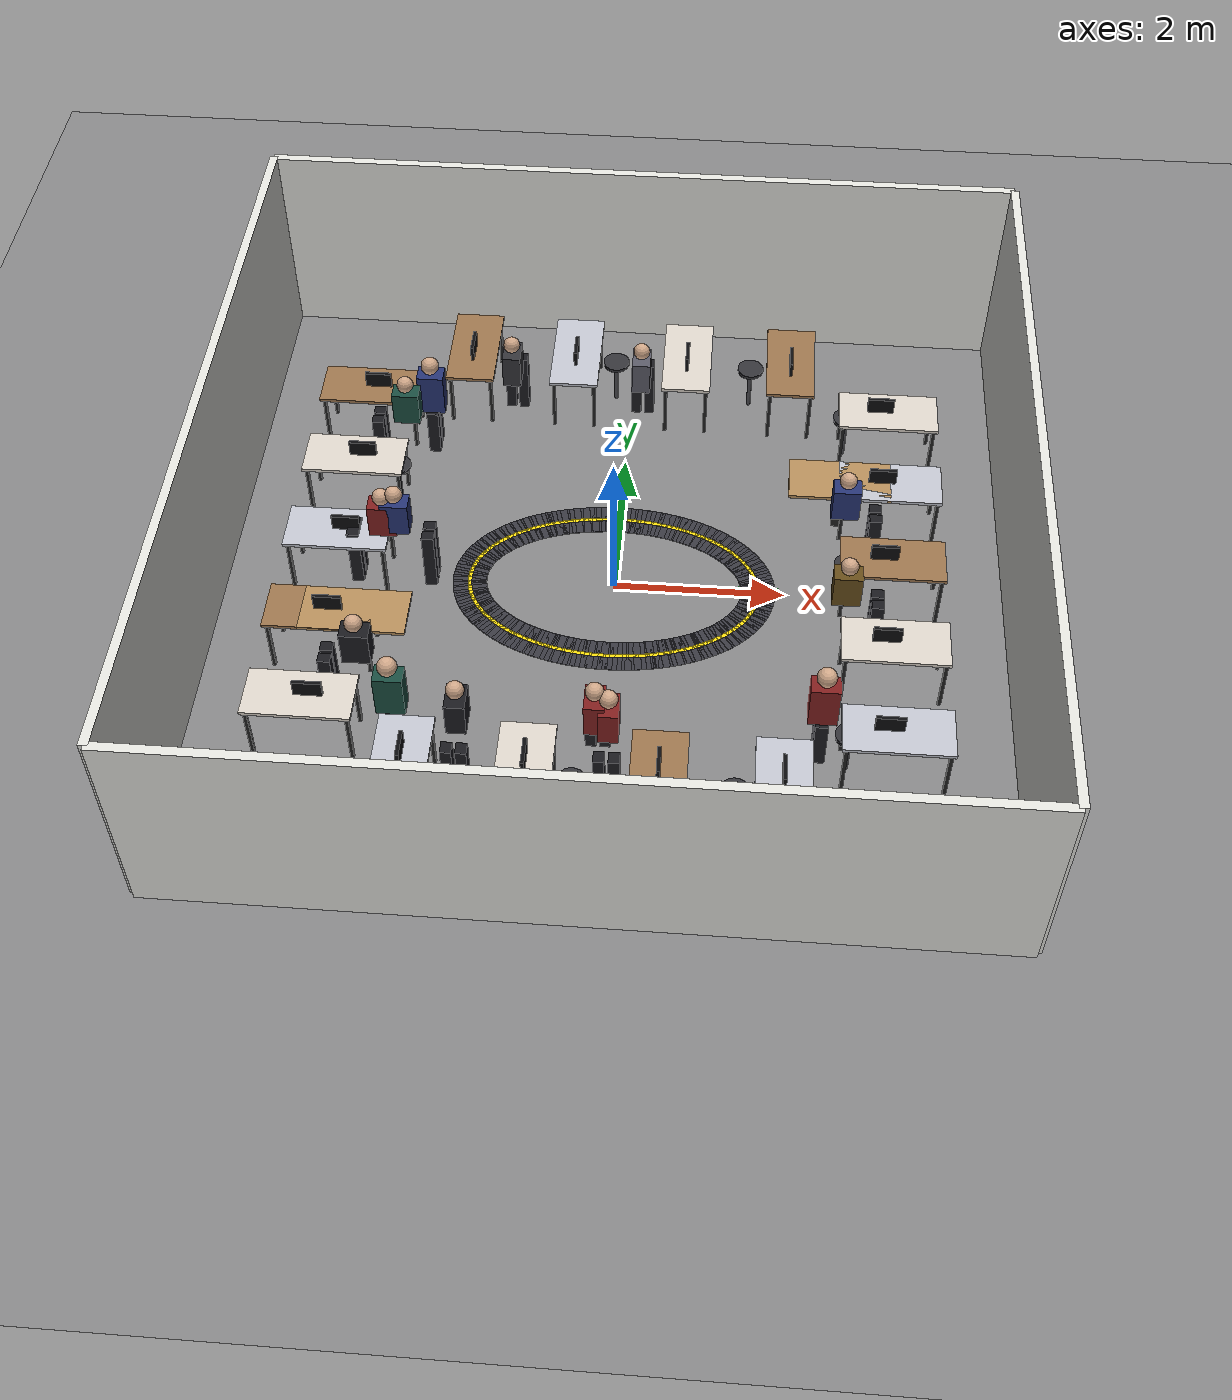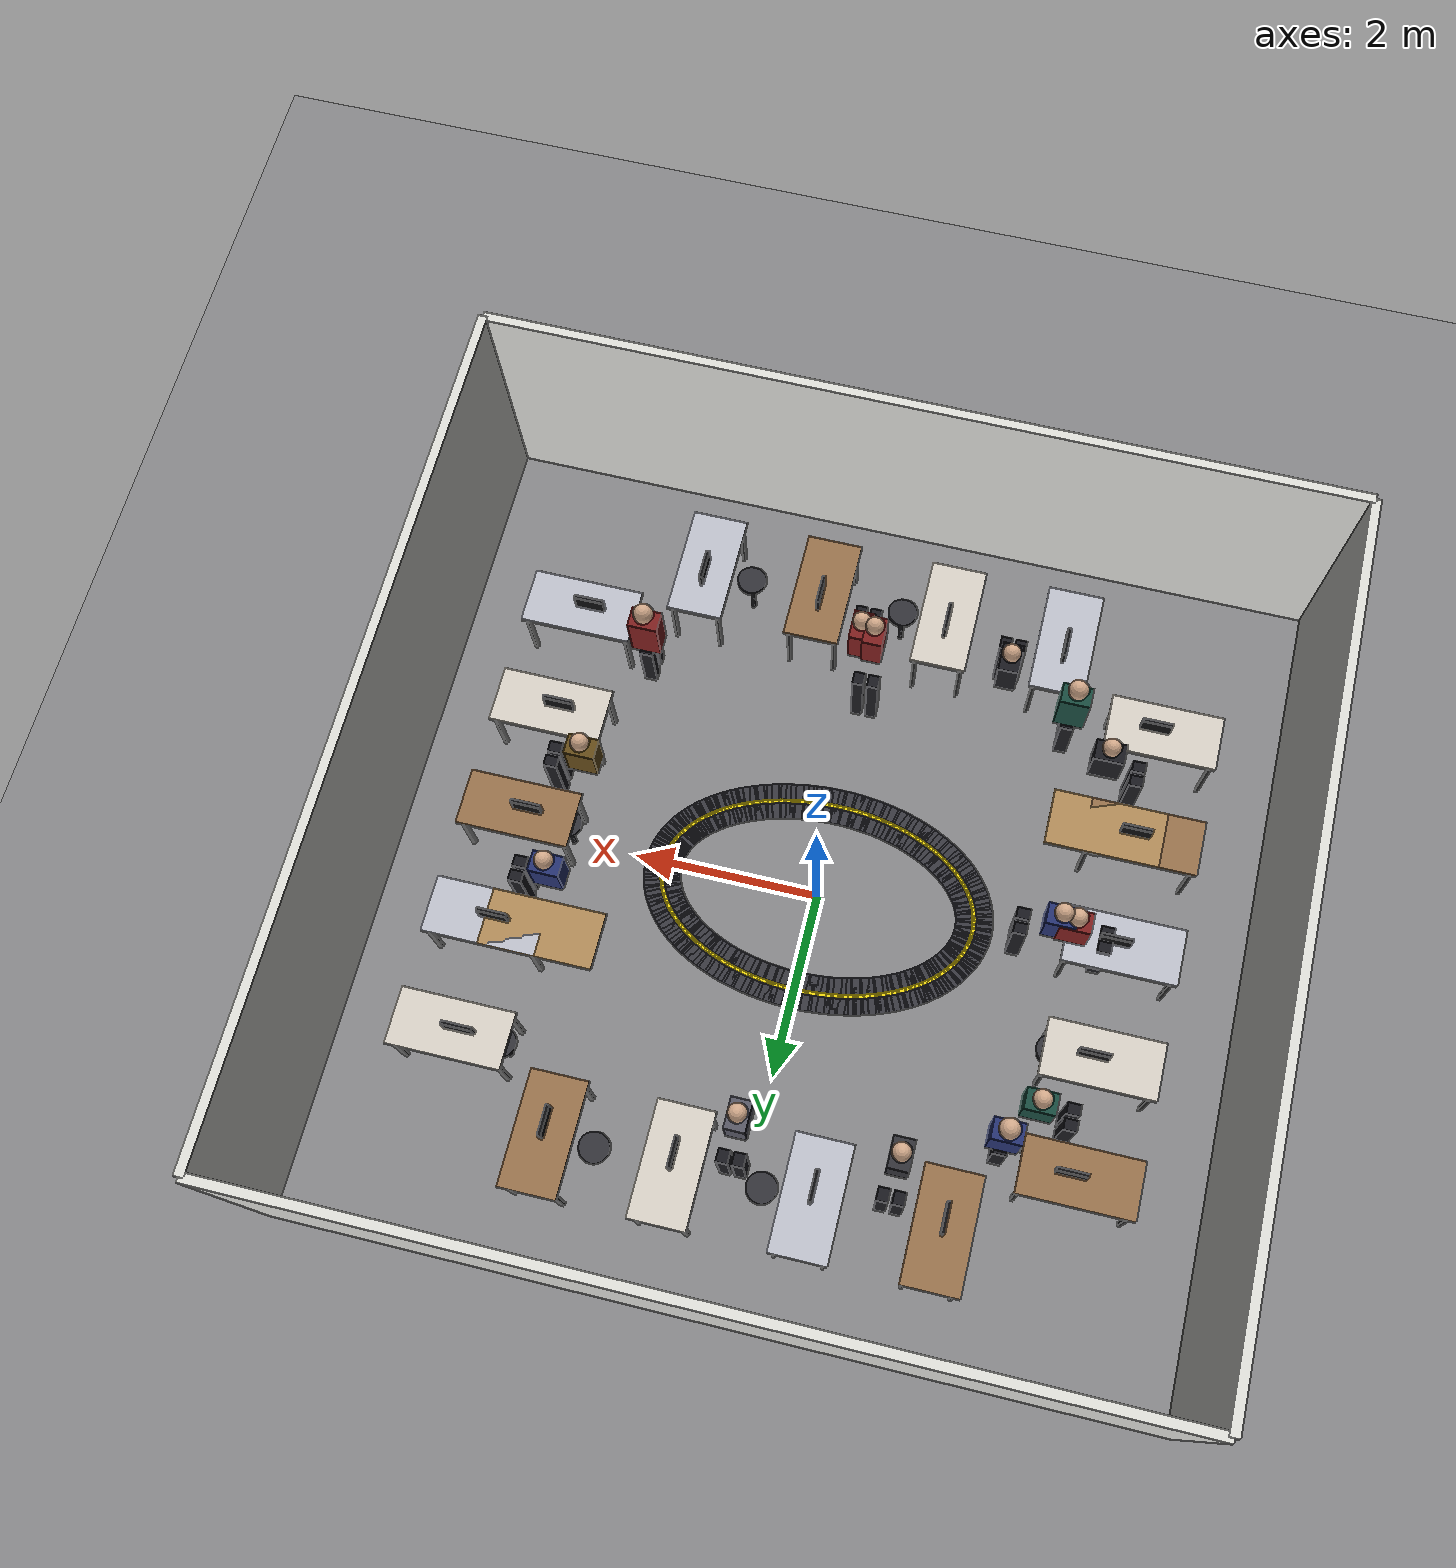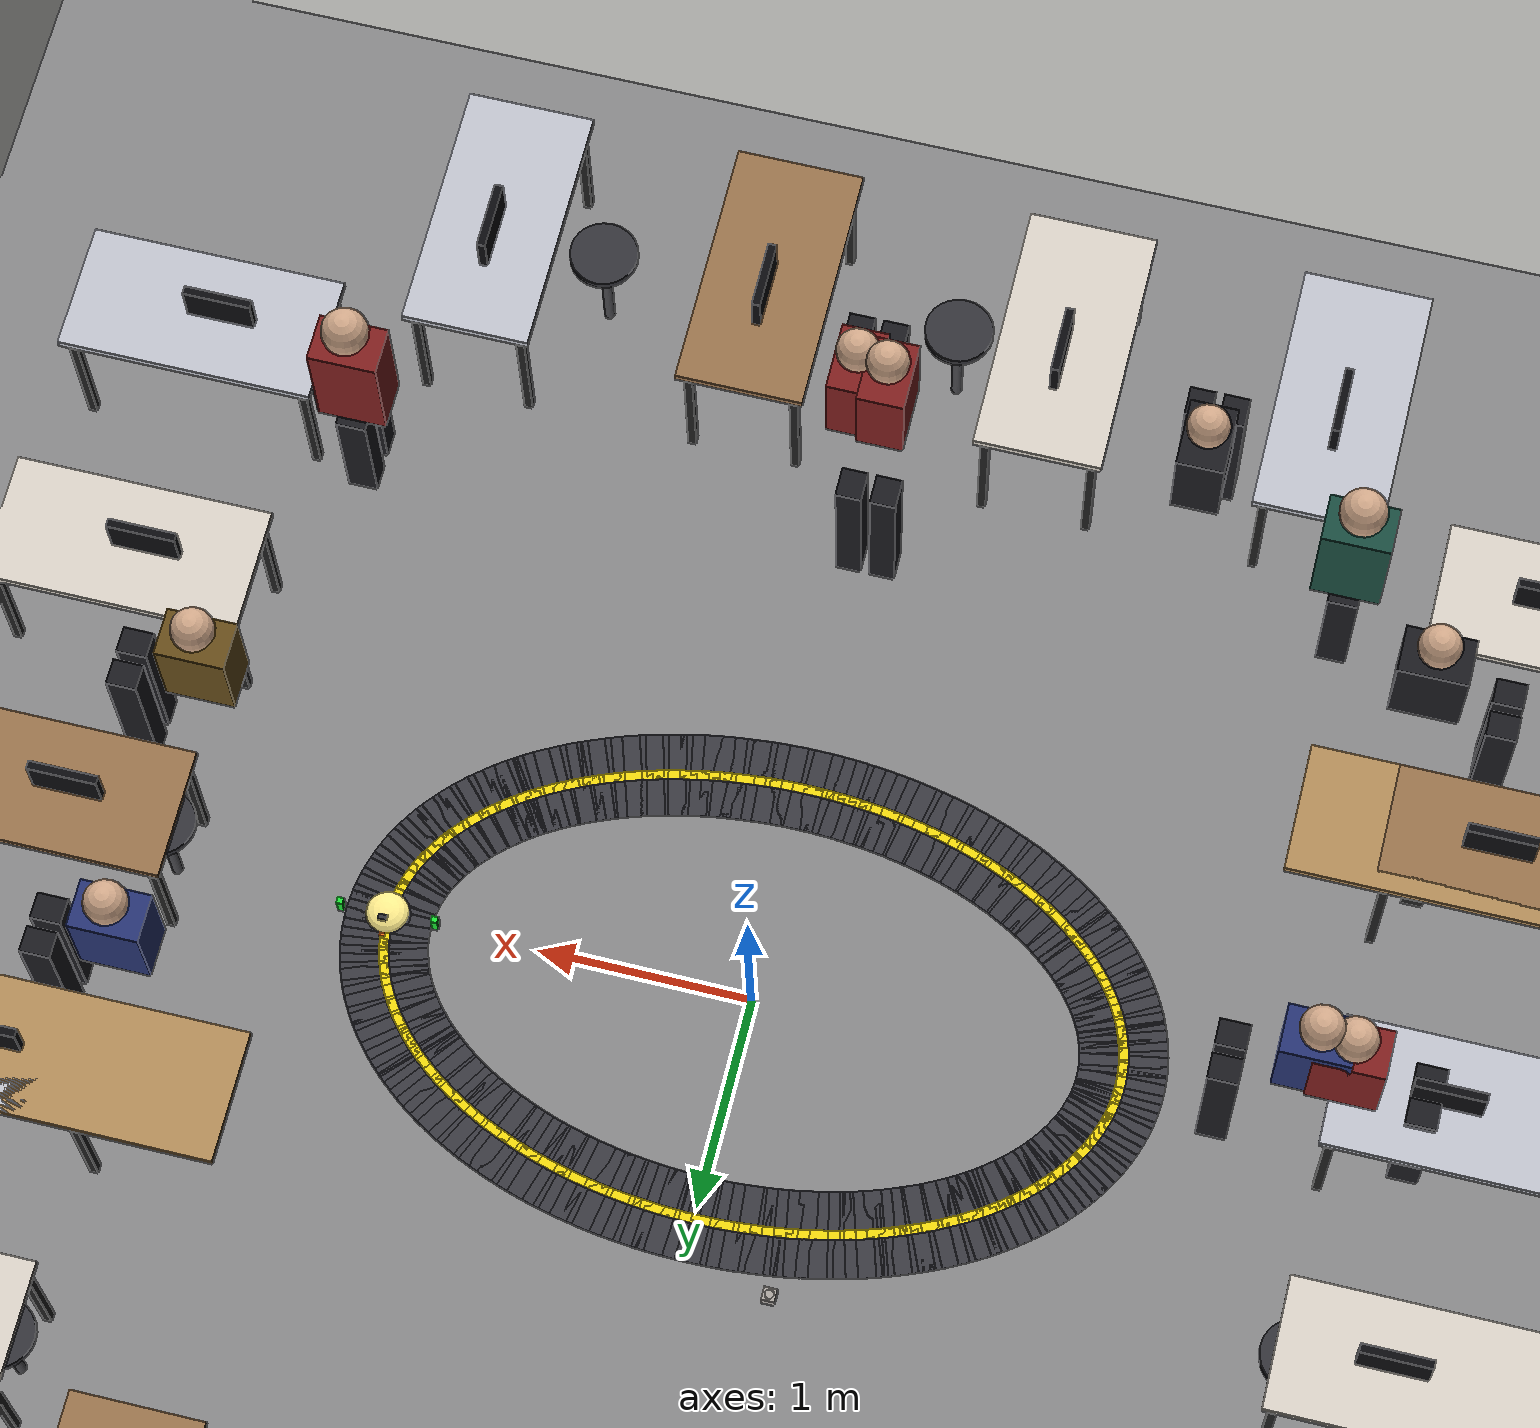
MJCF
<mujoco model="arena">
  <compiler angle="radian" autolimits="true" meshdir="meshes"/>
  <option timestep="0.002" integrator="implicitfast" gravity="0 0 -9.81"/>
  <default>
    <default class="wheel"><geom type="cylinder" size="0.028 0.01" zaxis="0 1 0"
      rgba="0.12 0.12 0.12 1" friction="1.4 0.01 0.001" condim="3"/>
      <joint type="hinge" axis="0 1 0" damping="0.015" armature="0.003"/></default>
    <default class="caster"><geom type="sphere" size="0.008" rgba="0.4 0.4 0.4 1" condim="1"/></default>
    <default class="camlink"><geom contype="0" conaffinity="0" rgba="0.2 0.2 0.22 1"/>
      <joint damping="0.6"/></default>
  </default>
  <visual>
    <global offwidth="1920" offheight="1080"/>
    <headlight diffuse="0.5 0.5 0.5" ambient="0.45 0.45 0.45"/>
    <quality shadowsize="2048" offsamples="4"/>
  </visual>
  <asset>
    <material name="floor" rgba="0.5 0.5 0.52 1" reflectance="0.05"/>
    <material name="wall" rgba="0.88 0.88 0.86 1"/>
    <mesh name="pyramid" file="pyramid.obj" scale="0.07 0.07 0.07"/>
    <mesh name="prism"   file="prism.obj"   scale="0.07 0.07 0.07"/>
    <texture name="t0" type="2d" file="textures/tex0.png"/>
    <material name="m0" texture="t0" texrepeat="2 2"/>
    <texture name="t1" type="2d" file="textures/tex1.png"/>
    <material name="m1" texture="t1" texrepeat="2 2"/>
    <texture name="t2" type="2d" file="textures/tex2.png"/>
    <material name="m2" texture="t2" texrepeat="2 2"/>
    <texture name="t3" type="2d" file="textures/tex3.png"/>
    <material name="m3" texture="t3" texrepeat="2 2"/>
    <texture name="t4" type="2d" file="textures/tex4.png"/>
    <material name="m4" texture="t4" texrepeat="2 2"/>
    <texture name="t5" type="2d" file="textures/tex5.png"/>
    <material name="m5" texture="t5" texrepeat="2 2"/>
    <texture name="t6" type="2d" file="textures/tex6.png"/>
    <material name="m6" texture="t6" texrepeat="2 2"/>
    <texture name="t7" type="2d" file="textures/tex7.png"/>
    <material name="m7" texture="t7" texrepeat="2 2"/>
  </asset>
  <worldbody>
    <light name="key"  pos="-2 -2 4" dir="0.5 0.5 -1" diffuse="0.6 0.6 0.6" castshadow="true"/>
    <light name="fill" pos="2 2 4"   dir="-0.5 -0.5 -1" diffuse="0.5 0.5 0.5" castshadow="false"/>
    <geom name="floor" type="plane" size="0 0 0.05" material="floor" condim="3" friction="1.0 0.005 0.0001"/>
    <geom type="box" pos="-4.6 0 1.3" size="0.05 4.5 1.3" material="wall"/>
    <geom type="box" pos=" 4.6 0 1.3" size="0.05 4.5 1.3" material="wall"/>
    <geom type="box" pos="0 -4.5 1.3" size="4.6 0.05 1.3" material="wall"/>
    <geom type="box" pos="0  4.5 1.3" size="4.6 0.05 1.3" material="wall"/>
    <body pos="-3.2 -2.4 0" euler="0 0 0.0">
      <geom type="box" pos="0 0 0.74" size="0.6 0.3 0.02" rgba="0.85 0.82 0.78 1"/>
      <geom type="box" pos="-0.55 -0.25 0.37" size="0.02 0.02 0.37" rgba="0.12 0.12 0.12 1"/>
      <geom type="box" pos="-0.55 0.25 0.37" size="0.02 0.02 0.37" rgba="0.12 0.12 0.12 1"/>
      <geom type="box" pos="0.55 -0.25 0.37" size="0.02 0.02 0.37" rgba="0.12 0.12 0.12 1"/>
      <geom type="box" pos="0.55 0.25 0.37" size="0.02 0.02 0.37" rgba="0.12 0.12 0.12 1"/>
      <geom type="box" pos="0.1 0 0.86" size="0.16 0.02 0.1" rgba="0.04 0.04 0.05 1"/>
    </body>
    <body pos="-2.6500000000000004 -1.8499999999999999 0" euler="0 0 3.1416">
      <geom type="box" pos="0 0 1.0" size="0.16 0.11 0.22" rgba="0.1 0.1 0.12 1"/>
      <geom type="sphere" pos="0 0 1.32" size="0.1" rgba="0.82 0.66 0.54 1"/>
      <geom type="box" pos="0.36 -0.08 0.4" size="0.07 0.06 0.4" rgba="0.1 0.1 0.12 1"/>
      <geom type="box" pos="0.36 0.08 0.4" size="0.07 0.06 0.4" rgba="0.1 0.1 0.12 1"/>
    </body>
    <body pos="-3.2 -1.2 0" euler="0 0 0.0">
      <geom type="box" pos="0 0 0.74" size="0.6 0.3 0.02" rgba="0.6 0.45 0.3 1"/>
      <geom type="box" pos="-0.55 -0.25 0.37" size="0.02 0.02 0.37" rgba="0.12 0.12 0.12 1"/>
      <geom type="box" pos="-0.55 0.25 0.37" size="0.02 0.02 0.37" rgba="0.12 0.12 0.12 1"/>
      <geom type="box" pos="0.55 -0.25 0.37" size="0.02 0.02 0.37" rgba="0.12 0.12 0.12 1"/>
      <geom type="box" pos="0.55 0.25 0.37" size="0.02 0.02 0.37" rgba="0.12 0.12 0.12 1"/>
      <geom type="box" pos="0.1 0 0.86" size="0.16 0.02 0.1" rgba="0.04 0.04 0.05 1"/>
    </body>
    <body pos="-2.7 -1.2 0"><geom type="cylinder" pos="0 0 0.6" size="0.16 0.02" rgba="0.2 0.2 0.22 1"/><geom type="cylinder" pos="0 0 0.3" size="0.025 0.3" rgba="0.3 0.3 0.32 1"/></body>
    <body pos="-3.2 0 0" euler="0 0 0.0">
      <geom type="box" pos="0 0 0.74" size="0.6 0.3 0.02" rgba="0.75 0.76 0.8 1"/>
      <geom type="box" pos="-0.55 -0.25 0.37" size="0.02 0.02 0.37" rgba="0.12 0.12 0.12 1"/>
      <geom type="box" pos="-0.55 0.25 0.37" size="0.02 0.02 0.37" rgba="0.12 0.12 0.12 1"/>
      <geom type="box" pos="0.55 -0.25 0.37" size="0.02 0.02 0.37" rgba="0.12 0.12 0.12 1"/>
      <geom type="box" pos="0.55 0.25 0.37" size="0.02 0.02 0.37" rgba="0.12 0.12 0.12 1"/>
      <geom type="box" pos="0.1 0 0.86" size="0.16 0.02 0.1" rgba="0.04 0.04 0.05 1"/>
    </body>
    <body pos="-2.6500000000000004 0 0" euler="0 0 3.1416">
      <geom type="box" pos="0 0 1.0" size="0.16 0.11 0.22" rgba="0.5 0.12 0.12 1"/>
      <geom type="sphere" pos="0 0 1.32" size="0.1" rgba="0.82 0.66 0.54 1"/>
      <geom type="box" pos="0.36 -0.08 0.4" size="0.07 0.06 0.4" rgba="0.1 0.1 0.12 1"/>
      <geom type="box" pos="0.36 0.08 0.4" size="0.07 0.06 0.4" rgba="0.1 0.1 0.12 1"/>
    </body>
    <body pos="-3.2 1.2 0" euler="0 0 0.0">
      <geom type="box" pos="0 0 0.74" size="0.6 0.3 0.02" rgba="0.85 0.82 0.78 1"/>
      <geom type="box" pos="-0.55 -0.25 0.37" size="0.02 0.02 0.37" rgba="0.12 0.12 0.12 1"/>
      <geom type="box" pos="-0.55 0.25 0.37" size="0.02 0.02 0.37" rgba="0.12 0.12 0.12 1"/>
      <geom type="box" pos="0.55 -0.25 0.37" size="0.02 0.02 0.37" rgba="0.12 0.12 0.12 1"/>
      <geom type="box" pos="0.55 0.25 0.37" size="0.02 0.02 0.37" rgba="0.12 0.12 0.12 1"/>
      <geom type="box" pos="0.1 0 0.86" size="0.16 0.02 0.1" rgba="0.04 0.04 0.05 1"/>
    </body>
    <body pos="-2.7 1.2 0"><geom type="cylinder" pos="0 0 0.6" size="0.16 0.02" rgba="0.2 0.2 0.22 1"/><geom type="cylinder" pos="0 0 0.3" size="0.025 0.3" rgba="0.3 0.3 0.32 1"/></body>
    <body pos="-3.2 2.4 0" euler="0 0 0.0">
      <geom type="box" pos="0 0 0.74" size="0.6 0.3 0.02" rgba="0.6 0.45 0.3 1"/>
      <geom type="box" pos="-0.55 -0.25 0.37" size="0.02 0.02 0.37" rgba="0.12 0.12 0.12 1"/>
      <geom type="box" pos="-0.55 0.25 0.37" size="0.02 0.02 0.37" rgba="0.12 0.12 0.12 1"/>
      <geom type="box" pos="0.55 -0.25 0.37" size="0.02 0.02 0.37" rgba="0.12 0.12 0.12 1"/>
      <geom type="box" pos="0.55 0.25 0.37" size="0.02 0.02 0.37" rgba="0.12 0.12 0.12 1"/>
      <geom type="box" pos="0.1 0 0.86" size="0.16 0.02 0.1" rgba="0.04 0.04 0.05 1"/>
    </body>
    <body pos="-2.6500000000000004 1.8499999999999999 0" euler="0 0 3.1416">
      <geom type="box" pos="0 0 1.0" size="0.16 0.11 0.22" rgba="0.1 0.3 0.25 1"/>
      <geom type="sphere" pos="0 0 1.32" size="0.1" rgba="0.82 0.66 0.54 1"/>
      <geom type="box" pos="0.36 -0.08 0.4" size="0.07 0.06 0.4" rgba="0.1 0.1 0.12 1"/>
      <geom type="box" pos="0.36 0.08 0.4" size="0.07 0.06 0.4" rgba="0.1 0.1 0.12 1"/>
    </body>
    <body pos="3.2 -2.4 0" euler="0 0 3.1416">
      <geom type="box" pos="0 0 0.74" size="0.6 0.3 0.02" rgba="0.75 0.76 0.8 1"/>
      <geom type="box" pos="-0.55 -0.25 0.37" size="0.02 0.02 0.37" rgba="0.12 0.12 0.12 1"/>
      <geom type="box" pos="-0.55 0.25 0.37" size="0.02 0.02 0.37" rgba="0.12 0.12 0.12 1"/>
      <geom type="box" pos="0.55 -0.25 0.37" size="0.02 0.02 0.37" rgba="0.12 0.12 0.12 1"/>
      <geom type="box" pos="0.55 0.25 0.37" size="0.02 0.02 0.37" rgba="0.12 0.12 0.12 1"/>
      <geom type="box" pos="0.1 0 0.86" size="0.16 0.02 0.1" rgba="0.04 0.04 0.05 1"/>
    </body>
    <body pos="2.7 -2.4 0"><geom type="cylinder" pos="0 0 0.6" size="0.16 0.02" rgba="0.2 0.2 0.22 1"/><geom type="cylinder" pos="0 0 0.3" size="0.025 0.3" rgba="0.3 0.3 0.32 1"/></body>
    <body pos="3.2 -1.2 0" euler="0 0 3.1416">
      <geom type="box" pos="0 0 0.74" size="0.6 0.3 0.02" rgba="0.85 0.82 0.78 1"/>
      <geom type="box" pos="-0.55 -0.25 0.37" size="0.02 0.02 0.37" rgba="0.12 0.12 0.12 1"/>
      <geom type="box" pos="-0.55 0.25 0.37" size="0.02 0.02 0.37" rgba="0.12 0.12 0.12 1"/>
      <geom type="box" pos="0.55 -0.25 0.37" size="0.02 0.02 0.37" rgba="0.12 0.12 0.12 1"/>
      <geom type="box" pos="0.55 0.25 0.37" size="0.02 0.02 0.37" rgba="0.12 0.12 0.12 1"/>
      <geom type="box" pos="0.1 0 0.86" size="0.16 0.02 0.1" rgba="0.04 0.04 0.05 1"/>
    </body>
    <body pos="2.6500000000000004 -0.6499999999999999 0" euler="0 0 6.2832">
      <geom type="box" pos="0 0 1.0" size="0.16 0.11 0.22" rgba="0.4 0.3 0.1 1"/>
      <geom type="sphere" pos="0 0 1.32" size="0.1" rgba="0.82 0.66 0.54 1"/>
      <geom type="box" pos="0.36 -0.08 0.4" size="0.07 0.06 0.4" rgba="0.1 0.1 0.12 1"/>
      <geom type="box" pos="0.36 0.08 0.4" size="0.07 0.06 0.4" rgba="0.1 0.1 0.12 1"/>
    </body>
    <body pos="3.2 0 0" euler="0 0 3.1416">
      <geom type="box" pos="0 0 0.74" size="0.6 0.3 0.02" rgba="0.6 0.45 0.3 1"/>
      <geom type="box" pos="-0.55 -0.25 0.37" size="0.02 0.02 0.37" rgba="0.12 0.12 0.12 1"/>
      <geom type="box" pos="-0.55 0.25 0.37" size="0.02 0.02 0.37" rgba="0.12 0.12 0.12 1"/>
      <geom type="box" pos="0.55 -0.25 0.37" size="0.02 0.02 0.37" rgba="0.12 0.12 0.12 1"/>
      <geom type="box" pos="0.55 0.25 0.37" size="0.02 0.02 0.37" rgba="0.12 0.12 0.12 1"/>
      <geom type="box" pos="0.1 0 0.86" size="0.16 0.02 0.1" rgba="0.04 0.04 0.05 1"/>
    </body>
    <body pos="2.7 0 0"><geom type="cylinder" pos="0 0 0.6" size="0.16 0.02" rgba="0.2 0.2 0.22 1"/><geom type="cylinder" pos="0 0 0.3" size="0.025 0.3" rgba="0.3 0.3 0.32 1"/></body>
    <body pos="3.2 1.2 0" euler="0 0 3.1416">
      <geom type="box" pos="0 0 0.74" size="0.6 0.3 0.02" rgba="0.75 0.76 0.8 1"/>
      <geom type="box" pos="-0.55 -0.25 0.37" size="0.02 0.02 0.37" rgba="0.12 0.12 0.12 1"/>
      <geom type="box" pos="-0.55 0.25 0.37" size="0.02 0.02 0.37" rgba="0.12 0.12 0.12 1"/>
      <geom type="box" pos="0.55 -0.25 0.37" size="0.02 0.02 0.37" rgba="0.12 0.12 0.12 1"/>
      <geom type="box" pos="0.55 0.25 0.37" size="0.02 0.02 0.37" rgba="0.12 0.12 0.12 1"/>
      <geom type="box" pos="0.1 0 0.86" size="0.16 0.02 0.1" rgba="0.04 0.04 0.05 1"/>
    </body>
    <body pos="2.6500000000000004 0.6499999999999999 0" euler="0 0 6.2832">
      <geom type="box" pos="0 0 1.0" size="0.16 0.11 0.22" rgba="0.15 0.2 0.45 1"/>
      <geom type="sphere" pos="0 0 1.32" size="0.1" rgba="0.82 0.66 0.54 1"/>
      <geom type="box" pos="0.36 -0.08 0.4" size="0.07 0.06 0.4" rgba="0.1 0.1 0.12 1"/>
      <geom type="box" pos="0.36 0.08 0.4" size="0.07 0.06 0.4" rgba="0.1 0.1 0.12 1"/>
    </body>
    <body pos="3.2 2.4 0" euler="0 0 3.1416">
      <geom type="box" pos="0 0 0.74" size="0.6 0.3 0.02" rgba="0.85 0.82 0.78 1"/>
      <geom type="box" pos="-0.55 -0.25 0.37" size="0.02 0.02 0.37" rgba="0.12 0.12 0.12 1"/>
      <geom type="box" pos="-0.55 0.25 0.37" size="0.02 0.02 0.37" rgba="0.12 0.12 0.12 1"/>
      <geom type="box" pos="0.55 -0.25 0.37" size="0.02 0.02 0.37" rgba="0.12 0.12 0.12 1"/>
      <geom type="box" pos="0.55 0.25 0.37" size="0.02 0.02 0.37" rgba="0.12 0.12 0.12 1"/>
      <geom type="box" pos="0.1 0 0.86" size="0.16 0.02 0.1" rgba="0.04 0.04 0.05 1"/>
    </body>
    <body pos="2.7 2.4 0"><geom type="cylinder" pos="0 0 0.6" size="0.16 0.02" rgba="0.2 0.2 0.22 1"/><geom type="cylinder" pos="0 0 0.3" size="0.025 0.3" rgba="0.3 0.3 0.32 1"/></body>
    <body pos="-2 3.2 0" euler="0 0 -1.5708">
      <geom type="box" pos="0 0 0.74" size="0.6 0.3 0.02" rgba="0.6 0.45 0.3 1"/>
      <geom type="box" pos="-0.55 -0.25 0.37" size="0.02 0.02 0.37" rgba="0.12 0.12 0.12 1"/>
      <geom type="box" pos="-0.55 0.25 0.37" size="0.02 0.02 0.37" rgba="0.12 0.12 0.12 1"/>
      <geom type="box" pos="0.55 -0.25 0.37" size="0.02 0.02 0.37" rgba="0.12 0.12 0.12 1"/>
      <geom type="box" pos="0.55 0.25 0.37" size="0.02 0.02 0.37" rgba="0.12 0.12 0.12 1"/>
      <geom type="box" pos="0.1 0 0.86" size="0.16 0.02 0.1" rgba="0.04 0.04 0.05 1"/>
    </body>
    <body pos="-1.45 2.6500000000000004 0" euler="0 0 1.5708">
      <geom type="box" pos="0 0 1.0" size="0.16 0.11 0.22" rgba="0.2 0.2 0.22 1"/>
      <geom type="sphere" pos="0 0 1.32" size="0.1" rgba="0.82 0.66 0.54 1"/>
      <geom type="box" pos="0.36 -0.08 0.4" size="0.07 0.06 0.4" rgba="0.1 0.1 0.12 1"/>
      <geom type="box" pos="0.36 0.08 0.4" size="0.07 0.06 0.4" rgba="0.1 0.1 0.12 1"/>
    </body>
    <body pos="-0.7 3.2 0" euler="0 0 -1.5708">
      <geom type="box" pos="0 0 0.74" size="0.6 0.3 0.02" rgba="0.75 0.76 0.8 1"/>
      <geom type="box" pos="-0.55 -0.25 0.37" size="0.02 0.02 0.37" rgba="0.12 0.12 0.12 1"/>
      <geom type="box" pos="-0.55 0.25 0.37" size="0.02 0.02 0.37" rgba="0.12 0.12 0.12 1"/>
      <geom type="box" pos="0.55 -0.25 0.37" size="0.02 0.02 0.37" rgba="0.12 0.12 0.12 1"/>
      <geom type="box" pos="0.55 0.25 0.37" size="0.02 0.02 0.37" rgba="0.12 0.12 0.12 1"/>
      <geom type="box" pos="0.1 0 0.86" size="0.16 0.02 0.1" rgba="0.04 0.04 0.05 1"/>
    </body>
    <body pos="-0.19999999999999996 3.2 0"><geom type="cylinder" pos="0 0 0.6" size="0.16 0.02" rgba="0.2 0.2 0.22 1"/><geom type="cylinder" pos="0 0 0.3" size="0.025 0.3" rgba="0.3 0.3 0.32 1"/></body>
    <body pos="0.7 3.2 0" euler="0 0 -1.5708">
      <geom type="box" pos="0 0 0.74" size="0.6 0.3 0.02" rgba="0.85 0.82 0.78 1"/>
      <geom type="box" pos="-0.55 -0.25 0.37" size="0.02 0.02 0.37" rgba="0.12 0.12 0.12 1"/>
      <geom type="box" pos="-0.55 0.25 0.37" size="0.02 0.02 0.37" rgba="0.12 0.12 0.12 1"/>
      <geom type="box" pos="0.55 -0.25 0.37" size="0.02 0.02 0.37" rgba="0.12 0.12 0.12 1"/>
      <geom type="box" pos="0.55 0.25 0.37" size="0.02 0.02 0.37" rgba="0.12 0.12 0.12 1"/>
      <geom type="box" pos="0.1 0 0.86" size="0.16 0.02 0.1" rgba="0.04 0.04 0.05 1"/>
    </body>
    <body pos="0.1499999999999999 2.6500000000000004 0" euler="0 0 1.5708">
      <geom type="box" pos="0 0 1.0" size="0.16 0.11 0.22" rgba="0.35 0.35 0.4 1"/>
      <geom type="sphere" pos="0 0 1.32" size="0.1" rgba="0.82 0.66 0.54 1"/>
      <geom type="box" pos="0.36 -0.08 0.4" size="0.07 0.06 0.4" rgba="0.1 0.1 0.12 1"/>
      <geom type="box" pos="0.36 0.08 0.4" size="0.07 0.06 0.4" rgba="0.1 0.1 0.12 1"/>
    </body>
    <body pos="2 3.2 0" euler="0 0 -1.5708">
      <geom type="box" pos="0 0 0.74" size="0.6 0.3 0.02" rgba="0.6 0.45 0.3 1"/>
      <geom type="box" pos="-0.55 -0.25 0.37" size="0.02 0.02 0.37" rgba="0.12 0.12 0.12 1"/>
      <geom type="box" pos="-0.55 0.25 0.37" size="0.02 0.02 0.37" rgba="0.12 0.12 0.12 1"/>
      <geom type="box" pos="0.55 -0.25 0.37" size="0.02 0.02 0.37" rgba="0.12 0.12 0.12 1"/>
      <geom type="box" pos="0.55 0.25 0.37" size="0.02 0.02 0.37" rgba="0.12 0.12 0.12 1"/>
      <geom type="box" pos="0.1 0 0.86" size="0.16 0.02 0.1" rgba="0.04 0.04 0.05 1"/>
    </body>
    <body pos="1.5 3.2 0"><geom type="cylinder" pos="0 0 0.6" size="0.16 0.02" rgba="0.2 0.2 0.22 1"/><geom type="cylinder" pos="0 0 0.3" size="0.025 0.3" rgba="0.3 0.3 0.32 1"/></body>
    <body pos="-2 -3.2 0" euler="0 0 1.5708">
      <geom type="box" pos="0 0 0.74" size="0.6 0.3 0.02" rgba="0.75 0.76 0.8 1"/>
      <geom type="box" pos="-0.55 -0.25 0.37" size="0.02 0.02 0.37" rgba="0.12 0.12 0.12 1"/>
      <geom type="box" pos="-0.55 0.25 0.37" size="0.02 0.02 0.37" rgba="0.12 0.12 0.12 1"/>
      <geom type="box" pos="0.55 -0.25 0.37" size="0.02 0.02 0.37" rgba="0.12 0.12 0.12 1"/>
      <geom type="box" pos="0.55 0.25 0.37" size="0.02 0.02 0.37" rgba="0.12 0.12 0.12 1"/>
      <geom type="box" pos="0.1 0 0.86" size="0.16 0.02 0.1" rgba="0.04 0.04 0.05 1"/>
    </body>
    <body pos="-1.45 -2.6500000000000004 0" euler="0 0 4.7124">
      <geom type="box" pos="0 0 1.0" size="0.16 0.11 0.22" rgba="0.1 0.1 0.12 1"/>
      <geom type="sphere" pos="0 0 1.32" size="0.1" rgba="0.82 0.66 0.54 1"/>
      <geom type="box" pos="0.36 -0.08 0.4" size="0.07 0.06 0.4" rgba="0.1 0.1 0.12 1"/>
      <geom type="box" pos="0.36 0.08 0.4" size="0.07 0.06 0.4" rgba="0.1 0.1 0.12 1"/>
    </body>
    <body pos="-0.7 -3.2 0" euler="0 0 1.5708">
      <geom type="box" pos="0 0 0.74" size="0.6 0.3 0.02" rgba="0.85 0.82 0.78 1"/>
      <geom type="box" pos="-0.55 -0.25 0.37" size="0.02 0.02 0.37" rgba="0.12 0.12 0.12 1"/>
      <geom type="box" pos="-0.55 0.25 0.37" size="0.02 0.02 0.37" rgba="0.12 0.12 0.12 1"/>
      <geom type="box" pos="0.55 -0.25 0.37" size="0.02 0.02 0.37" rgba="0.12 0.12 0.12 1"/>
      <geom type="box" pos="0.55 0.25 0.37" size="0.02 0.02 0.37" rgba="0.12 0.12 0.12 1"/>
      <geom type="box" pos="0.1 0 0.86" size="0.16 0.02 0.1" rgba="0.04 0.04 0.05 1"/>
    </body>
    <body pos="-0.19999999999999996 -3.2 0"><geom type="cylinder" pos="0 0 0.6" size="0.16 0.02" rgba="0.2 0.2 0.22 1"/><geom type="cylinder" pos="0 0 0.3" size="0.025 0.3" rgba="0.3 0.3 0.32 1"/></body>
    <body pos="0.7 -3.2 0" euler="0 0 1.5708">
      <geom type="box" pos="0 0 0.74" size="0.6 0.3 0.02" rgba="0.6 0.45 0.3 1"/>
      <geom type="box" pos="-0.55 -0.25 0.37" size="0.02 0.02 0.37" rgba="0.12 0.12 0.12 1"/>
      <geom type="box" pos="-0.55 0.25 0.37" size="0.02 0.02 0.37" rgba="0.12 0.12 0.12 1"/>
      <geom type="box" pos="0.55 -0.25 0.37" size="0.02 0.02 0.37" rgba="0.12 0.12 0.12 1"/>
      <geom type="box" pos="0.55 0.25 0.37" size="0.02 0.02 0.37" rgba="0.12 0.12 0.12 1"/>
      <geom type="box" pos="0.1 0 0.86" size="0.16 0.02 0.1" rgba="0.04 0.04 0.05 1"/>
    </body>
    <body pos="0.1499999999999999 -2.6500000000000004 0" euler="0 0 4.7124">
      <geom type="box" pos="0 0 1.0" size="0.16 0.11 0.22" rgba="0.5 0.12 0.12 1"/>
      <geom type="sphere" pos="0 0 1.32" size="0.1" rgba="0.82 0.66 0.54 1"/>
      <geom type="box" pos="0.36 -0.08 0.4" size="0.07 0.06 0.4" rgba="0.1 0.1 0.12 1"/>
      <geom type="box" pos="0.36 0.08 0.4" size="0.07 0.06 0.4" rgba="0.1 0.1 0.12 1"/>
    </body>
    <body pos="2 -3.2 0" euler="0 0 1.5708">
      <geom type="box" pos="0 0 0.74" size="0.6 0.3 0.02" rgba="0.75 0.76 0.8 1"/>
      <geom type="box" pos="-0.55 -0.25 0.37" size="0.02 0.02 0.37" rgba="0.12 0.12 0.12 1"/>
      <geom type="box" pos="-0.55 0.25 0.37" size="0.02 0.02 0.37" rgba="0.12 0.12 0.12 1"/>
      <geom type="box" pos="0.55 -0.25 0.37" size="0.02 0.02 0.37" rgba="0.12 0.12 0.12 1"/>
      <geom type="box" pos="0.55 0.25 0.37" size="0.02 0.02 0.37" rgba="0.12 0.12 0.12 1"/>
      <geom type="box" pos="0.1 0 0.86" size="0.16 0.02 0.1" rgba="0.04 0.04 0.05 1"/>
    </body>
    <body pos="1.5 -3.2 0"><geom type="cylinder" pos="0 0 0.6" size="0.16 0.02" rgba="0.2 0.2 0.22 1"/><geom type="cylinder" pos="0 0 0.3" size="0.025 0.3" rgba="0.3 0.3 0.32 1"/></body>
    <body pos="0 -2.6 0" euler="0 0 1.5708">
      <geom type="box" pos="0 0 1.05" size="0.16 0.11 0.22" rgba="0.5 0.12 0.12 1"/>
      <geom type="sphere" pos="0 0 1.37" size="0.1" rgba="0.82 0.66 0.54 1"/>
      <geom type="box" pos="0.36 -0.08 0.4" size="0.07 0.06 0.4" rgba="0.1 0.1 0.12 1"/>
      <geom type="box" pos="0.36 0.08 0.4" size="0.07 0.06 0.4" rgba="0.1 0.1 0.12 1"/>
    </body>
    <body pos="-2.5 0 0" euler="0 0 0">
      <geom type="box" pos="0 0 1.05" size="0.16 0.11 0.22" rgba="0.15 0.2 0.45 1"/>
      <geom type="sphere" pos="0 0 1.37" size="0.1" rgba="0.82 0.66 0.54 1"/>
      <geom type="box" pos="0.36 -0.08 0.4" size="0.07 0.06 0.4" rgba="0.1 0.1 0.12 1"/>
      <geom type="box" pos="0.36 0.08 0.4" size="0.07 0.06 0.4" rgba="0.1 0.1 0.12 1"/>
    </body>
    <geom name="start_l" type="box" pos="1.480 -0.006 0.05" size="0.015 0.015 0.05" rgba="0.1 0.9 0.2 1" contype="0" conaffinity="0"/>
    <geom name="start_r" type="box" pos="1.920 0.006 0.05" size="0.015 0.015 0.05" rgba="0.1 0.9 0.2 1" contype="0" conaffinity="0"/>
    <geom type="box" pos="1.700 0.016 0.001" euler="0 0 1.596" size="0.026 0.200 0.001" rgba="0.22 0.22 0.25 1" contype="0" conaffinity="0"/>
    <geom type="box" pos="1.698 0.049 0.001" euler="0 0 1.647" size="0.026 0.200 0.001" rgba="0.22 0.22 0.25 1" contype="0" conaffinity="0"/>
    <geom type="box" pos="1.695 0.082 0.001" euler="0 0 1.698" size="0.027 0.200 0.001" rgba="0.22 0.22 0.25 1" contype="0" conaffinity="0"/>
    <geom type="box" pos="1.690 0.115 0.001" euler="0 0 1.748" size="0.027 0.200 0.001" rgba="0.22 0.22 0.25 1" contype="0" conaffinity="0"/>
    <geom type="box" pos="1.683 0.148 0.001" euler="0 0 1.797" size="0.027 0.200 0.001" rgba="0.22 0.22 0.25 1" contype="0" conaffinity="0"/>
    <geom type="box" pos="1.674 0.181 0.001" euler="0 0 1.846" size="0.027 0.200 0.001" rgba="0.22 0.22 0.25 1" contype="0" conaffinity="0"/>
    <geom type="box" pos="1.664 0.213 0.001" euler="0 0 1.894" size="0.027 0.200 0.001" rgba="0.22 0.22 0.25 1" contype="0" conaffinity="0"/>
    <geom type="box" pos="1.653 0.245 0.001" euler="0 0 1.942" size="0.028 0.200 0.001" rgba="0.22 0.22 0.25 1" contype="0" conaffinity="0"/>
    <geom type="box" pos="1.640 0.277 0.001" euler="0 0 1.988" size="0.028 0.200 0.001" rgba="0.22 0.22 0.25 1" contype="0" conaffinity="0"/>
    <geom type="box" pos="1.625 0.309 0.001" euler="0 0 2.033" size="0.028 0.200 0.001" rgba="0.22 0.22 0.25 1" contype="0" conaffinity="0"/>
    <geom type="box" pos="1.608 0.340 0.001" euler="0 0 2.077" size="0.029 0.200 0.001" rgba="0.22 0.22 0.25 1" contype="0" conaffinity="0"/>
    <geom type="box" pos="1.590 0.371 0.001" euler="0 0 2.120" size="0.029 0.200 0.001" rgba="0.22 0.22 0.25 1" contype="0" conaffinity="0"/>
    <geom type="box" pos="1.570 0.402 0.001" euler="0 0 2.162" size="0.029 0.200 0.001" rgba="0.22 0.22 0.25 1" contype="0" conaffinity="0"/>
    <geom type="box" pos="1.549 0.432 0.001" euler="0 0 2.202" size="0.030 0.200 0.001" rgba="0.22 0.22 0.25 1" contype="0" conaffinity="0"/>
    <geom type="box" pos="1.526 0.462 0.001" euler="0 0 2.241" size="0.030 0.200 0.001" rgba="0.22 0.22 0.25 1" contype="0" conaffinity="0"/>
    <geom type="box" pos="1.502 0.491 0.001" euler="0 0 2.279" size="0.031 0.200 0.001" rgba="0.22 0.22 0.25 1" contype="0" conaffinity="0"/>
    <geom type="box" pos="1.476 0.520 0.001" euler="0 0 2.316" size="0.031 0.200 0.001" rgba="0.22 0.22 0.25 1" contype="0" conaffinity="0"/>
    <geom type="box" pos="1.449 0.549 0.001" euler="0 0 2.352" size="0.032 0.200 0.001" rgba="0.22 0.22 0.25 1" contype="0" conaffinity="0"/>
    <geom type="box" pos="1.421 0.576 0.001" euler="0 0 2.387" size="0.032 0.200 0.001" rgba="0.22 0.22 0.25 1" contype="0" conaffinity="0"/>
    <geom type="box" pos="1.391 0.604 0.001" euler="0 0 2.421" size="0.033 0.200 0.001" rgba="0.22 0.22 0.25 1" contype="0" conaffinity="0"/>
    <geom type="box" pos="1.359 0.630 0.001" euler="0 0 2.453" size="0.033 0.200 0.001" rgba="0.22 0.22 0.25 1" contype="0" conaffinity="0"/>
    <geom type="box" pos="1.327 0.656 0.001" euler="0 0 2.485" size="0.034 0.200 0.001" rgba="0.22 0.22 0.25 1" contype="0" conaffinity="0"/>
    <geom type="box" pos="1.293 0.682 0.001" euler="0 0 2.515" size="0.034 0.200 0.001" rgba="0.22 0.22 0.25 1" contype="0" conaffinity="0"/>
    <geom type="box" pos="1.257 0.707 0.001" euler="0 0 2.545" size="0.035 0.200 0.001" rgba="0.22 0.22 0.25 1" contype="0" conaffinity="0"/>
    <geom type="box" pos="1.221 0.731 0.001" euler="0 0 2.574" size="0.035 0.200 0.001" rgba="0.22 0.22 0.25 1" contype="0" conaffinity="0"/>
    <geom type="box" pos="1.183 0.754 0.001" euler="0 0 2.602" size="0.036 0.200 0.001" rgba="0.22 0.22 0.25 1" contype="0" conaffinity="0"/>
    <geom type="box" pos="1.144 0.777 0.001" euler="0 0 2.630" size="0.036 0.200 0.001" rgba="0.22 0.22 0.25 1" contype="0" conaffinity="0"/>
    <geom type="box" pos="1.104 0.798 0.001" euler="0 0 2.656" size="0.037 0.200 0.001" rgba="0.22 0.22 0.25 1" contype="0" conaffinity="0"/>
    <geom type="box" pos="1.063 0.819 0.001" euler="0 0 2.682" size="0.037 0.200 0.001" rgba="0.22 0.22 0.25 1" contype="0" conaffinity="0"/>
    <geom type="box" pos="1.021 0.840 0.001" euler="0 0 2.707" size="0.038 0.200 0.001" rgba="0.22 0.22 0.25 1" contype="0" conaffinity="0"/>
    <geom type="box" pos="0.977 0.859 0.001" euler="0 0 2.732" size="0.038 0.200 0.001" rgba="0.22 0.22 0.25 1" contype="0" conaffinity="0"/>
    <geom type="box" pos="0.933 0.877 0.001" euler="0 0 2.756" size="0.039 0.200 0.001" rgba="0.22 0.22 0.25 1" contype="0" conaffinity="0"/>
    <geom type="box" pos="0.888 0.895 0.001" euler="0 0 2.780" size="0.039 0.200 0.001" rgba="0.22 0.22 0.25 1" contype="0" conaffinity="0"/>
    <geom type="box" pos="0.842 0.912 0.001" euler="0 0 2.803" size="0.039 0.200 0.001" rgba="0.22 0.22 0.25 1" contype="0" conaffinity="0"/>
    <geom type="box" pos="0.795 0.928 0.001" euler="0 0 2.826" size="0.040 0.200 0.001" rgba="0.22 0.22 0.25 1" contype="0" conaffinity="0"/>
    <geom type="box" pos="0.748 0.943 0.001" euler="0 0 2.848" size="0.040 0.200 0.001" rgba="0.22 0.22 0.25 1" contype="0" conaffinity="0"/>
    <geom type="box" pos="0.699 0.957 0.001" euler="0 0 2.870" size="0.040 0.200 0.001" rgba="0.22 0.22 0.25 1" contype="0" conaffinity="0"/>
    <geom type="box" pos="0.650 0.970 0.001" euler="0 0 2.891" size="0.041 0.200 0.001" rgba="0.22 0.22 0.25 1" contype="0" conaffinity="0"/>
    <geom type="box" pos="0.601 0.982 0.001" euler="0 0 2.912" size="0.041 0.200 0.001" rgba="0.22 0.22 0.25 1" contype="0" conaffinity="0"/>
    <geom type="box" pos="0.551 0.993 0.001" euler="0 0 2.933" size="0.041 0.200 0.001" rgba="0.22 0.22 0.25 1" contype="0" conaffinity="0"/>
    <geom type="box" pos="0.500 1.003 0.001" euler="0 0 2.954" size="0.042 0.200 0.001" rgba="0.22 0.22 0.25 1" contype="0" conaffinity="0"/>
    <geom type="box" pos="0.449 1.013 0.001" euler="0 0 2.974" size="0.042 0.200 0.001" rgba="0.22 0.22 0.25 1" contype="0" conaffinity="0"/>
    <geom type="box" pos="0.397 1.021 0.001" euler="0 0 2.994" size="0.042 0.200 0.001" rgba="0.22 0.22 0.25 1" contype="0" conaffinity="0"/>
    <geom type="box" pos="0.345 1.028 0.001" euler="0 0 3.014" size="0.042 0.200 0.001" rgba="0.22 0.22 0.25 1" contype="0" conaffinity="0"/>
    <geom type="box" pos="0.292 1.034 0.001" euler="0 0 3.034" size="0.042 0.200 0.001" rgba="0.22 0.22 0.25 1" contype="0" conaffinity="0"/>
    <geom type="box" pos="0.240 1.039 0.001" euler="0 0 3.054" size="0.042 0.200 0.001" rgba="0.22 0.22 0.25 1" contype="0" conaffinity="0"/>
    <geom type="box" pos="0.187 1.044 0.001" euler="0 0 3.074" size="0.043 0.200 0.001" rgba="0.22 0.22 0.25 1" contype="0" conaffinity="0"/>
    <geom type="box" pos="0.133 1.047 0.001" euler="0 0 3.093" size="0.043 0.200 0.001" rgba="0.22 0.22 0.25 1" contype="0" conaffinity="0"/>
    <geom type="box" pos="0.080 1.049 0.001" euler="0 0 3.112" size="0.043 0.200 0.001" rgba="0.22 0.22 0.25 1" contype="0" conaffinity="0"/>
    <geom type="box" pos="0.027 1.050 0.001" euler="0 0 3.132" size="0.043 0.200 0.001" rgba="0.22 0.22 0.25 1" contype="0" conaffinity="0"/>
    <geom type="box" pos="-0.027 1.050 0.001" euler="0 0 -3.132" size="0.043 0.200 0.001" rgba="0.22 0.22 0.25 1" contype="0" conaffinity="0"/>
    <geom type="box" pos="-0.080 1.049 0.001" euler="0 0 -3.112" size="0.043 0.200 0.001" rgba="0.22 0.22 0.25 1" contype="0" conaffinity="0"/>
    <geom type="box" pos="-0.133 1.047 0.001" euler="0 0 -3.093" size="0.043 0.200 0.001" rgba="0.22 0.22 0.25 1" contype="0" conaffinity="0"/>
    <geom type="box" pos="-0.187 1.044 0.001" euler="0 0 -3.074" size="0.043 0.200 0.001" rgba="0.22 0.22 0.25 1" contype="0" conaffinity="0"/>
    <geom type="box" pos="-0.240 1.039 0.001" euler="0 0 -3.054" size="0.042 0.200 0.001" rgba="0.22 0.22 0.25 1" contype="0" conaffinity="0"/>
    <geom type="box" pos="-0.292 1.034 0.001" euler="0 0 -3.034" size="0.042 0.200 0.001" rgba="0.22 0.22 0.25 1" contype="0" conaffinity="0"/>
    <geom type="box" pos="-0.345 1.028 0.001" euler="0 0 -3.014" size="0.042 0.200 0.001" rgba="0.22 0.22 0.25 1" contype="0" conaffinity="0"/>
    <geom type="box" pos="-0.397 1.021 0.001" euler="0 0 -2.994" size="0.042 0.200 0.001" rgba="0.22 0.22 0.25 1" contype="0" conaffinity="0"/>
    <geom type="box" pos="-0.449 1.013 0.001" euler="0 0 -2.974" size="0.042 0.200 0.001" rgba="0.22 0.22 0.25 1" contype="0" conaffinity="0"/>
    <geom type="box" pos="-0.500 1.003 0.001" euler="0 0 -2.954" size="0.042 0.200 0.001" rgba="0.22 0.22 0.25 1" contype="0" conaffinity="0"/>
    <geom type="box" pos="-0.551 0.993 0.001" euler="0 0 -2.933" size="0.041 0.200 0.001" rgba="0.22 0.22 0.25 1" contype="0" conaffinity="0"/>
    <geom type="box" pos="-0.601 0.982 0.001" euler="0 0 -2.912" size="0.041 0.200 0.001" rgba="0.22 0.22 0.25 1" contype="0" conaffinity="0"/>
    <geom type="box" pos="-0.650 0.970 0.001" euler="0 0 -2.891" size="0.041 0.200 0.001" rgba="0.22 0.22 0.25 1" contype="0" conaffinity="0"/>
    <geom type="box" pos="-0.699 0.957 0.001" euler="0 0 -2.870" size="0.040 0.200 0.001" rgba="0.22 0.22 0.25 1" contype="0" conaffinity="0"/>
    <geom type="box" pos="-0.748 0.943 0.001" euler="0 0 -2.848" size="0.040 0.200 0.001" rgba="0.22 0.22 0.25 1" contype="0" conaffinity="0"/>
    <geom type="box" pos="-0.795 0.928 0.001" euler="0 0 -2.826" size="0.040 0.200 0.001" rgba="0.22 0.22 0.25 1" contype="0" conaffinity="0"/>
    <geom type="box" pos="-0.842 0.912 0.001" euler="0 0 -2.803" size="0.039 0.200 0.001" rgba="0.22 0.22 0.25 1" contype="0" conaffinity="0"/>
    <geom type="box" pos="-0.888 0.895 0.001" euler="0 0 -2.780" size="0.039 0.200 0.001" rgba="0.22 0.22 0.25 1" contype="0" conaffinity="0"/>
    <geom type="box" pos="-0.933 0.877 0.001" euler="0 0 -2.756" size="0.039 0.200 0.001" rgba="0.22 0.22 0.25 1" contype="0" conaffinity="0"/>
    <geom type="box" pos="-0.977 0.859 0.001" euler="0 0 -2.732" size="0.038 0.200 0.001" rgba="0.22 0.22 0.25 1" contype="0" conaffinity="0"/>
    <geom type="box" pos="-1.021 0.840 0.001" euler="0 0 -2.707" size="0.038 0.200 0.001" rgba="0.22 0.22 0.25 1" contype="0" conaffinity="0"/>
    <geom type="box" pos="-1.063 0.819 0.001" euler="0 0 -2.682" size="0.037 0.200 0.001" rgba="0.22 0.22 0.25 1" contype="0" conaffinity="0"/>
    <geom type="box" pos="-1.104 0.798 0.001" euler="0 0 -2.656" size="0.037 0.200 0.001" rgba="0.22 0.22 0.25 1" contype="0" conaffinity="0"/>
    <geom type="box" pos="-1.144 0.777 0.001" euler="0 0 -2.630" size="0.036 0.200 0.001" rgba="0.22 0.22 0.25 1" contype="0" conaffinity="0"/>
    <geom type="box" pos="-1.183 0.754 0.001" euler="0 0 -2.602" size="0.036 0.200 0.001" rgba="0.22 0.22 0.25 1" contype="0" conaffinity="0"/>
    <geom type="box" pos="-1.221 0.731 0.001" euler="0 0 -2.574" size="0.035 0.200 0.001" rgba="0.22 0.22 0.25 1" contype="0" conaffinity="0"/>
    <geom type="box" pos="-1.257 0.707 0.001" euler="0 0 -2.545" size="0.035 0.200 0.001" rgba="0.22 0.22 0.25 1" contype="0" conaffinity="0"/>
    <geom type="box" pos="-1.293 0.682 0.001" euler="0 0 -2.515" size="0.034 0.200 0.001" rgba="0.22 0.22 0.25 1" contype="0" conaffinity="0"/>
    <geom type="box" pos="-1.327 0.656 0.001" euler="0 0 -2.485" size="0.034 0.200 0.001" rgba="0.22 0.22 0.25 1" contype="0" conaffinity="0"/>
    <geom type="box" pos="-1.359 0.630 0.001" euler="0 0 -2.453" size="0.033 0.200 0.001" rgba="0.22 0.22 0.25 1" contype="0" conaffinity="0"/>
    <geom type="box" pos="-1.391 0.604 0.001" euler="0 0 -2.421" size="0.033 0.200 0.001" rgba="0.22 0.22 0.25 1" contype="0" conaffinity="0"/>
    <geom type="box" pos="-1.421 0.576 0.001" euler="0 0 -2.387" size="0.032 0.200 0.001" rgba="0.22 0.22 0.25 1" contype="0" conaffinity="0"/>
    <geom type="box" pos="-1.449 0.549 0.001" euler="0 0 -2.352" size="0.032 0.200 0.001" rgba="0.22 0.22 0.25 1" contype="0" conaffinity="0"/>
    <geom type="box" pos="-1.476 0.520 0.001" euler="0 0 -2.316" size="0.031 0.200 0.001" rgba="0.22 0.22 0.25 1" contype="0" conaffinity="0"/>
    <geom type="box" pos="-1.502 0.491 0.001" euler="0 0 -2.279" size="0.031 0.200 0.001" rgba="0.22 0.22 0.25 1" contype="0" conaffinity="0"/>
    <geom type="box" pos="-1.526 0.462 0.001" euler="0 0 -2.241" size="0.030 0.200 0.001" rgba="0.22 0.22 0.25 1" contype="0" conaffinity="0"/>
    <geom type="box" pos="-1.549 0.432 0.001" euler="0 0 -2.202" size="0.030 0.200 0.001" rgba="0.22 0.22 0.25 1" contype="0" conaffinity="0"/>
    <geom type="box" pos="-1.570 0.402 0.001" euler="0 0 -2.162" size="0.029 0.200 0.001" rgba="0.22 0.22 0.25 1" contype="0" conaffinity="0"/>
    <geom type="box" pos="-1.590 0.371 0.001" euler="0 0 -2.120" size="0.029 0.200 0.001" rgba="0.22 0.22 0.25 1" contype="0" conaffinity="0"/>
    <geom type="box" pos="-1.608 0.340 0.001" euler="0 0 -2.077" size="0.029 0.200 0.001" rgba="0.22 0.22 0.25 1" contype="0" conaffinity="0"/>
    <geom type="box" pos="-1.625 0.309 0.001" euler="0 0 -2.033" size="0.028 0.200 0.001" rgba="0.22 0.22 0.25 1" contype="0" conaffinity="0"/>
    <geom type="box" pos="-1.640 0.277 0.001" euler="0 0 -1.988" size="0.028 0.200 0.001" rgba="0.22 0.22 0.25 1" contype="0" conaffinity="0"/>
    <geom type="box" pos="-1.653 0.245 0.001" euler="0 0 -1.942" size="0.028 0.200 0.001" rgba="0.22 0.22 0.25 1" contype="0" conaffinity="0"/>
    <geom type="box" pos="-1.664 0.213 0.001" euler="0 0 -1.894" size="0.027 0.200 0.001" rgba="0.22 0.22 0.25 1" contype="0" conaffinity="0"/>
    <geom type="box" pos="-1.674 0.181 0.001" euler="0 0 -1.846" size="0.027 0.200 0.001" rgba="0.22 0.22 0.25 1" contype="0" conaffinity="0"/>
    <geom type="box" pos="-1.683 0.148 0.001" euler="0 0 -1.797" size="0.027 0.200 0.001" rgba="0.22 0.22 0.25 1" contype="0" conaffinity="0"/>
    <geom type="box" pos="-1.690 0.115 0.001" euler="0 0 -1.748" size="0.027 0.200 0.001" rgba="0.22 0.22 0.25 1" contype="0" conaffinity="0"/>
    <geom type="box" pos="-1.695 0.082 0.001" euler="0 0 -1.698" size="0.027 0.200 0.001" rgba="0.22 0.22 0.25 1" contype="0" conaffinity="0"/>
    <geom type="box" pos="-1.698 0.049 0.001" euler="0 0 -1.647" size="0.026 0.200 0.001" rgba="0.22 0.22 0.25 1" contype="0" conaffinity="0"/>
    <geom type="box" pos="-1.700 0.016 0.001" euler="0 0 -1.596" size="0.026 0.200 0.001" rgba="0.22 0.22 0.25 1" contype="0" conaffinity="0"/>
    <geom type="box" pos="-1.700 -0.016 0.001" euler="0 0 -1.545" size="0.026 0.200 0.001" rgba="0.22 0.22 0.25 1" contype="0" conaffinity="0"/>
    <geom type="box" pos="-1.698 -0.049 0.001" euler="0 0 -1.495" size="0.026 0.200 0.001" rgba="0.22 0.22 0.25 1" contype="0" conaffinity="0"/>
    <geom type="box" pos="-1.695 -0.082 0.001" euler="0 0 -1.444" size="0.027 0.200 0.001" rgba="0.22 0.22 0.25 1" contype="0" conaffinity="0"/>
    <geom type="box" pos="-1.690 -0.115 0.001" euler="0 0 -1.394" size="0.027 0.200 0.001" rgba="0.22 0.22 0.25 1" contype="0" conaffinity="0"/>
    <geom type="box" pos="-1.683 -0.148 0.001" euler="0 0 -1.344" size="0.027 0.200 0.001" rgba="0.22 0.22 0.25 1" contype="0" conaffinity="0"/>
    <geom type="box" pos="-1.674 -0.181 0.001" euler="0 0 -1.295" size="0.027 0.200 0.001" rgba="0.22 0.22 0.25 1" contype="0" conaffinity="0"/>
    <geom type="box" pos="-1.664 -0.213 0.001" euler="0 0 -1.247" size="0.027 0.200 0.001" rgba="0.22 0.22 0.25 1" contype="0" conaffinity="0"/>
    <geom type="box" pos="-1.653 -0.245 0.001" euler="0 0 -1.200" size="0.028 0.200 0.001" rgba="0.22 0.22 0.25 1" contype="0" conaffinity="0"/>
    <geom type="box" pos="-1.640 -0.277 0.001" euler="0 0 -1.154" size="0.028 0.200 0.001" rgba="0.22 0.22 0.25 1" contype="0" conaffinity="0"/>
    <geom type="box" pos="-1.625 -0.309 0.001" euler="0 0 -1.109" size="0.028 0.200 0.001" rgba="0.22 0.22 0.25 1" contype="0" conaffinity="0"/>
    <geom type="box" pos="-1.608 -0.340 0.001" euler="0 0 -1.065" size="0.029 0.200 0.001" rgba="0.22 0.22 0.25 1" contype="0" conaffinity="0"/>
    <geom type="box" pos="-1.590 -0.371 0.001" euler="0 0 -1.022" size="0.029 0.200 0.001" rgba="0.22 0.22 0.25 1" contype="0" conaffinity="0"/>
    <geom type="box" pos="-1.570 -0.402 0.001" euler="0 0 -0.980" size="0.029 0.200 0.001" rgba="0.22 0.22 0.25 1" contype="0" conaffinity="0"/>
    <geom type="box" pos="-1.549 -0.432 0.001" euler="0 0 -0.940" size="0.030 0.200 0.001" rgba="0.22 0.22 0.25 1" contype="0" conaffinity="0"/>
    <geom type="box" pos="-1.526 -0.462 0.001" euler="0 0 -0.900" size="0.030 0.200 0.001" rgba="0.22 0.22 0.25 1" contype="0" conaffinity="0"/>
    <geom type="box" pos="-1.502 -0.491 0.001" euler="0 0 -0.862" size="0.031 0.200 0.001" rgba="0.22 0.22 0.25 1" contype="0" conaffinity="0"/>
    <geom type="box" pos="-1.476 -0.520 0.001" euler="0 0 -0.825" size="0.031 0.200 0.001" rgba="0.22 0.22 0.25 1" contype="0" conaffinity="0"/>
    <geom type="box" pos="-1.449 -0.549 0.001" euler="0 0 -0.789" size="0.032 0.200 0.001" rgba="0.22 0.22 0.25 1" contype="0" conaffinity="0"/>
    <geom type="box" pos="-1.421 -0.576 0.001" euler="0 0 -0.755" size="0.032 0.200 0.001" rgba="0.22 0.22 0.25 1" contype="0" conaffinity="0"/>
    <geom type="box" pos="-1.391 -0.604 0.001" euler="0 0 -0.721" size="0.033 0.200 0.001" rgba="0.22 0.22 0.25 1" contype="0" conaffinity="0"/>
    <geom type="box" pos="-1.359 -0.630 0.001" euler="0 0 -0.688" size="0.033 0.200 0.001" rgba="0.22 0.22 0.25 1" contype="0" conaffinity="0"/>
    <geom type="box" pos="-1.327 -0.656 0.001" euler="0 0 -0.657" size="0.034 0.200 0.001" rgba="0.22 0.22 0.25 1" contype="0" conaffinity="0"/>
    <geom type="box" pos="-1.293 -0.682 0.001" euler="0 0 -0.626" size="0.034 0.200 0.001" rgba="0.22 0.22 0.25 1" contype="0" conaffinity="0"/>
    <geom type="box" pos="-1.257 -0.707 0.001" euler="0 0 -0.596" size="0.035 0.200 0.001" rgba="0.22 0.22 0.25 1" contype="0" conaffinity="0"/>
    <geom type="box" pos="-1.221 -0.731 0.001" euler="0 0 -0.567" size="0.035 0.200 0.001" rgba="0.22 0.22 0.25 1" contype="0" conaffinity="0"/>
    <geom type="box" pos="-1.183 -0.754 0.001" euler="0 0 -0.539" size="0.036 0.200 0.001" rgba="0.22 0.22 0.25 1" contype="0" conaffinity="0"/>
    <geom type="box" pos="-1.144 -0.777 0.001" euler="0 0 -0.512" size="0.036 0.200 0.001" rgba="0.22 0.22 0.25 1" contype="0" conaffinity="0"/>
    <geom type="box" pos="-1.104 -0.798 0.001" euler="0 0 -0.485" size="0.037 0.200 0.001" rgba="0.22 0.22 0.25 1" contype="0" conaffinity="0"/>
    <geom type="box" pos="-1.063 -0.819 0.001" euler="0 0 -0.460" size="0.037 0.200 0.001" rgba="0.22 0.22 0.25 1" contype="0" conaffinity="0"/>
    <geom type="box" pos="-1.021 -0.840 0.001" euler="0 0 -0.434" size="0.038 0.200 0.001" rgba="0.22 0.22 0.25 1" contype="0" conaffinity="0"/>
    <geom type="box" pos="-0.977 -0.859 0.001" euler="0 0 -0.410" size="0.038 0.200 0.001" rgba="0.22 0.22 0.25 1" contype="0" conaffinity="0"/>
    <geom type="box" pos="-0.933 -0.877 0.001" euler="0 0 -0.385" size="0.039 0.200 0.001" rgba="0.22 0.22 0.25 1" contype="0" conaffinity="0"/>
    <geom type="box" pos="-0.888 -0.895 0.001" euler="0 0 -0.362" size="0.039 0.200 0.001" rgba="0.22 0.22 0.25 1" contype="0" conaffinity="0"/>
    <geom type="box" pos="-0.842 -0.912 0.001" euler="0 0 -0.339" size="0.039 0.200 0.001" rgba="0.22 0.22 0.25 1" contype="0" conaffinity="0"/>
    <geom type="box" pos="-0.795 -0.928 0.001" euler="0 0 -0.316" size="0.040 0.200 0.001" rgba="0.22 0.22 0.25 1" contype="0" conaffinity="0"/>
    <geom type="box" pos="-0.748 -0.943 0.001" euler="0 0 -0.294" size="0.040 0.200 0.001" rgba="0.22 0.22 0.25 1" contype="0" conaffinity="0"/>
    <geom type="box" pos="-0.699 -0.957 0.001" euler="0 0 -0.272" size="0.040 0.200 0.001" rgba="0.22 0.22 0.25 1" contype="0" conaffinity="0"/>
    <geom type="box" pos="-0.650 -0.970 0.001" euler="0 0 -0.250" size="0.041 0.200 0.001" rgba="0.22 0.22 0.25 1" contype="0" conaffinity="0"/>
    <geom type="box" pos="-0.601 -0.982 0.001" euler="0 0 -0.229" size="0.041 0.200 0.001" rgba="0.22 0.22 0.25 1" contype="0" conaffinity="0"/>
    <geom type="box" pos="-0.551 -0.993 0.001" euler="0 0 -0.208" size="0.041 0.200 0.001" rgba="0.22 0.22 0.25 1" contype="0" conaffinity="0"/>
    <geom type="box" pos="-0.500 -1.003 0.001" euler="0 0 -0.188" size="0.042 0.200 0.001" rgba="0.22 0.22 0.25 1" contype="0" conaffinity="0"/>
    <geom type="box" pos="-0.449 -1.013 0.001" euler="0 0 -0.167" size="0.042 0.200 0.001" rgba="0.22 0.22 0.25 1" contype="0" conaffinity="0"/>
    <geom type="box" pos="-0.397 -1.021 0.001" euler="0 0 -0.147" size="0.042 0.200 0.001" rgba="0.22 0.22 0.25 1" contype="0" conaffinity="0"/>
    <geom type="box" pos="-0.345 -1.028 0.001" euler="0 0 -0.127" size="0.042 0.200 0.001" rgba="0.22 0.22 0.25 1" contype="0" conaffinity="0"/>
    <geom type="box" pos="-0.292 -1.034 0.001" euler="0 0 -0.107" size="0.042 0.200 0.001" rgba="0.22 0.22 0.25 1" contype="0" conaffinity="0"/>
    <geom type="box" pos="-0.240 -1.039 0.001" euler="0 0 -0.088" size="0.042 0.200 0.001" rgba="0.22 0.22 0.25 1" contype="0" conaffinity="0"/>
    <geom type="box" pos="-0.187 -1.044 0.001" euler="0 0 -0.068" size="0.043 0.200 0.001" rgba="0.22 0.22 0.25 1" contype="0" conaffinity="0"/>
    <geom type="box" pos="-0.133 -1.047 0.001" euler="0 0 -0.049" size="0.043 0.200 0.001" rgba="0.22 0.22 0.25 1" contype="0" conaffinity="0"/>
    <geom type="box" pos="-0.080 -1.049 0.001" euler="0 0 -0.029" size="0.043 0.200 0.001" rgba="0.22 0.22 0.25 1" contype="0" conaffinity="0"/>
    <geom type="box" pos="-0.027 -1.050 0.001" euler="0 0 -0.010" size="0.043 0.200 0.001" rgba="0.22 0.22 0.25 1" contype="0" conaffinity="0"/>
    <geom type="box" pos="0.027 -1.050 0.001" euler="0 0 0.010" size="0.043 0.200 0.001" rgba="0.22 0.22 0.25 1" contype="0" conaffinity="0"/>
    <geom type="box" pos="0.080 -1.049 0.001" euler="0 0 0.029" size="0.043 0.200 0.001" rgba="0.22 0.22 0.25 1" contype="0" conaffinity="0"/>
    <geom type="box" pos="0.133 -1.047 0.001" euler="0 0 0.049" size="0.043 0.200 0.001" rgba="0.22 0.22 0.25 1" contype="0" conaffinity="0"/>
    <geom type="box" pos="0.187 -1.044 0.001" euler="0 0 0.068" size="0.043 0.200 0.001" rgba="0.22 0.22 0.25 1" contype="0" conaffinity="0"/>
    <geom type="box" pos="0.240 -1.039 0.001" euler="0 0 0.088" size="0.042 0.200 0.001" rgba="0.22 0.22 0.25 1" contype="0" conaffinity="0"/>
    <geom type="box" pos="0.292 -1.034 0.001" euler="0 0 0.107" size="0.042 0.200 0.001" rgba="0.22 0.22 0.25 1" contype="0" conaffinity="0"/>
    <geom type="box" pos="0.345 -1.028 0.001" euler="0 0 0.127" size="0.042 0.200 0.001" rgba="0.22 0.22 0.25 1" contype="0" conaffinity="0"/>
    <geom type="box" pos="0.397 -1.021 0.001" euler="0 0 0.147" size="0.042 0.200 0.001" rgba="0.22 0.22 0.25 1" contype="0" conaffinity="0"/>
    <geom type="box" pos="0.449 -1.013 0.001" euler="0 0 0.167" size="0.042 0.200 0.001" rgba="0.22 0.22 0.25 1" contype="0" conaffinity="0"/>
    <geom type="box" pos="0.500 -1.003 0.001" euler="0 0 0.188" size="0.042 0.200 0.001" rgba="0.22 0.22 0.25 1" contype="0" conaffinity="0"/>
    <geom type="box" pos="0.551 -0.993 0.001" euler="0 0 0.208" size="0.041 0.200 0.001" rgba="0.22 0.22 0.25 1" contype="0" conaffinity="0"/>
    <geom type="box" pos="0.601 -0.982 0.001" euler="0 0 0.229" size="0.041 0.200 0.001" rgba="0.22 0.22 0.25 1" contype="0" conaffinity="0"/>
    <geom type="box" pos="0.650 -0.970 0.001" euler="0 0 0.250" size="0.041 0.200 0.001" rgba="0.22 0.22 0.25 1" contype="0" conaffinity="0"/>
    <geom type="box" pos="0.699 -0.957 0.001" euler="0 0 0.272" size="0.040 0.200 0.001" rgba="0.22 0.22 0.25 1" contype="0" conaffinity="0"/>
    <geom type="box" pos="0.748 -0.943 0.001" euler="0 0 0.294" size="0.040 0.200 0.001" rgba="0.22 0.22 0.25 1" contype="0" conaffinity="0"/>
    <geom type="box" pos="0.795 -0.928 0.001" euler="0 0 0.316" size="0.040 0.200 0.001" rgba="0.22 0.22 0.25 1" contype="0" conaffinity="0"/>
    <geom type="box" pos="0.842 -0.912 0.001" euler="0 0 0.339" size="0.039 0.200 0.001" rgba="0.22 0.22 0.25 1" contype="0" conaffinity="0"/>
    <geom type="box" pos="0.888 -0.895 0.001" euler="0 0 0.362" size="0.039 0.200 0.001" rgba="0.22 0.22 0.25 1" contype="0" conaffinity="0"/>
    <geom type="box" pos="0.933 -0.877 0.001" euler="0 0 0.385" size="0.039 0.200 0.001" rgba="0.22 0.22 0.25 1" contype="0" conaffinity="0"/>
    <geom type="box" pos="0.977 -0.859 0.001" euler="0 0 0.410" size="0.038 0.200 0.001" rgba="0.22 0.22 0.25 1" contype="0" conaffinity="0"/>
    <geom type="box" pos="1.021 -0.840 0.001" euler="0 0 0.434" size="0.038 0.200 0.001" rgba="0.22 0.22 0.25 1" contype="0" conaffinity="0"/>
    <geom type="box" pos="1.063 -0.819 0.001" euler="0 0 0.460" size="0.037 0.200 0.001" rgba="0.22 0.22 0.25 1" contype="0" conaffinity="0"/>
    <geom type="box" pos="1.104 -0.798 0.001" euler="0 0 0.485" size="0.037 0.200 0.001" rgba="0.22 0.22 0.25 1" contype="0" conaffinity="0"/>
    <geom type="box" pos="1.144 -0.777 0.001" euler="0 0 0.512" size="0.036 0.200 0.001" rgba="0.22 0.22 0.25 1" contype="0" conaffinity="0"/>
    <geom type="box" pos="1.183 -0.754 0.001" euler="0 0 0.539" size="0.036 0.200 0.001" rgba="0.22 0.22 0.25 1" contype="0" conaffinity="0"/>
    <geom type="box" pos="1.221 -0.731 0.001" euler="0 0 0.567" size="0.035 0.200 0.001" rgba="0.22 0.22 0.25 1" contype="0" conaffinity="0"/>
    <geom type="box" pos="1.257 -0.707 0.001" euler="0 0 0.596" size="0.035 0.200 0.001" rgba="0.22 0.22 0.25 1" contype="0" conaffinity="0"/>
    <geom type="box" pos="1.293 -0.682 0.001" euler="0 0 0.626" size="0.034 0.200 0.001" rgba="0.22 0.22 0.25 1" contype="0" conaffinity="0"/>
    <geom type="box" pos="1.327 -0.656 0.001" euler="0 0 0.657" size="0.034 0.200 0.001" rgba="0.22 0.22 0.25 1" contype="0" conaffinity="0"/>
    <geom type="box" pos="1.359 -0.630 0.001" euler="0 0 0.688" size="0.033 0.200 0.001" rgba="0.22 0.22 0.25 1" contype="0" conaffinity="0"/>
    <geom type="box" pos="1.391 -0.604 0.001" euler="0 0 0.721" size="0.033 0.200 0.001" rgba="0.22 0.22 0.25 1" contype="0" conaffinity="0"/>
    <geom type="box" pos="1.421 -0.576 0.001" euler="0 0 0.755" size="0.032 0.200 0.001" rgba="0.22 0.22 0.25 1" contype="0" conaffinity="0"/>
    <geom type="box" pos="1.449 -0.549 0.001" euler="0 0 0.789" size="0.032 0.200 0.001" rgba="0.22 0.22 0.25 1" contype="0" conaffinity="0"/>
    <geom type="box" pos="1.476 -0.520 0.001" euler="0 0 0.825" size="0.031 0.200 0.001" rgba="0.22 0.22 0.25 1" contype="0" conaffinity="0"/>
    <geom type="box" pos="1.502 -0.491 0.001" euler="0 0 0.862" size="0.031 0.200 0.001" rgba="0.22 0.22 0.25 1" contype="0" conaffinity="0"/>
    <geom type="box" pos="1.526 -0.462 0.001" euler="0 0 0.900" size="0.030 0.200 0.001" rgba="0.22 0.22 0.25 1" contype="0" conaffinity="0"/>
    <geom type="box" pos="1.549 -0.432 0.001" euler="0 0 0.940" size="0.030 0.200 0.001" rgba="0.22 0.22 0.25 1" contype="0" conaffinity="0"/>
    <geom type="box" pos="1.570 -0.402 0.001" euler="0 0 0.980" size="0.029 0.200 0.001" rgba="0.22 0.22 0.25 1" contype="0" conaffinity="0"/>
    <geom type="box" pos="1.590 -0.371 0.001" euler="0 0 1.022" size="0.029 0.200 0.001" rgba="0.22 0.22 0.25 1" contype="0" conaffinity="0"/>
    <geom type="box" pos="1.608 -0.340 0.001" euler="0 0 1.065" size="0.029 0.200 0.001" rgba="0.22 0.22 0.25 1" contype="0" conaffinity="0"/>
    <geom type="box" pos="1.625 -0.309 0.001" euler="0 0 1.109" size="0.028 0.200 0.001" rgba="0.22 0.22 0.25 1" contype="0" conaffinity="0"/>
    <geom type="box" pos="1.640 -0.277 0.001" euler="0 0 1.154" size="0.028 0.200 0.001" rgba="0.22 0.22 0.25 1" contype="0" conaffinity="0"/>
    <geom type="box" pos="1.653 -0.245 0.001" euler="0 0 1.200" size="0.028 0.200 0.001" rgba="0.22 0.22 0.25 1" contype="0" conaffinity="0"/>
    <geom type="box" pos="1.664 -0.213 0.001" euler="0 0 1.247" size="0.027 0.200 0.001" rgba="0.22 0.22 0.25 1" contype="0" conaffinity="0"/>
    <geom type="box" pos="1.674 -0.181 0.001" euler="0 0 1.295" size="0.027 0.200 0.001" rgba="0.22 0.22 0.25 1" contype="0" conaffinity="0"/>
    <geom type="box" pos="1.683 -0.148 0.001" euler="0 0 1.344" size="0.027 0.200 0.001" rgba="0.22 0.22 0.25 1" contype="0" conaffinity="0"/>
    <geom type="box" pos="1.690 -0.115 0.001" euler="0 0 1.394" size="0.027 0.200 0.001" rgba="0.22 0.22 0.25 1" contype="0" conaffinity="0"/>
    <geom type="box" pos="1.695 -0.082 0.001" euler="0 0 1.444" size="0.027 0.200 0.001" rgba="0.22 0.22 0.25 1" contype="0" conaffinity="0"/>
    <geom type="box" pos="1.698 -0.049 0.001" euler="0 0 1.495" size="0.026 0.200 0.001" rgba="0.22 0.22 0.25 1" contype="0" conaffinity="0"/>
    <geom type="box" pos="1.700 -0.016 0.001" euler="0 0 1.545" size="0.026 0.200 0.001" rgba="0.22 0.22 0.25 1" contype="0" conaffinity="0"/>
    <geom type="box" pos="1.700 0.016 0.0025" euler="0 0 1.596" size="0.026 0.022 0.0012" rgba="0.95 0.85 0.05 1" contype="0" conaffinity="0"/>
    <geom type="box" pos="1.698 0.049 0.0025" euler="0 0 1.647" size="0.026 0.022 0.0012" rgba="0.95 0.85 0.05 1" contype="0" conaffinity="0"/>
    <geom type="box" pos="1.695 0.082 0.0025" euler="0 0 1.698" size="0.027 0.022 0.0012" rgba="0.95 0.85 0.05 1" contype="0" conaffinity="0"/>
    <geom type="box" pos="1.690 0.115 0.0025" euler="0 0 1.748" size="0.027 0.022 0.0012" rgba="0.95 0.85 0.05 1" contype="0" conaffinity="0"/>
    <geom type="box" pos="1.683 0.148 0.0025" euler="0 0 1.797" size="0.027 0.022 0.0012" rgba="0.95 0.85 0.05 1" contype="0" conaffinity="0"/>
    <geom type="box" pos="1.674 0.181 0.0025" euler="0 0 1.846" size="0.027 0.022 0.0012" rgba="0.95 0.85 0.05 1" contype="0" conaffinity="0"/>
    <geom type="box" pos="1.664 0.213 0.0025" euler="0 0 1.894" size="0.027 0.022 0.0012" rgba="0.95 0.85 0.05 1" contype="0" conaffinity="0"/>
    <geom type="box" pos="1.653 0.245 0.0025" euler="0 0 1.942" size="0.028 0.022 0.0012" rgba="0.95 0.85 0.05 1" contype="0" conaffinity="0"/>
    <geom type="box" pos="1.640 0.277 0.0025" euler="0 0 1.988" size="0.028 0.022 0.0012" rgba="0.95 0.85 0.05 1" contype="0" conaffinity="0"/>
    <geom type="box" pos="1.625 0.309 0.0025" euler="0 0 2.033" size="0.028 0.022 0.0012" rgba="0.95 0.85 0.05 1" contype="0" conaffinity="0"/>
    <geom type="box" pos="1.608 0.340 0.0025" euler="0 0 2.077" size="0.029 0.022 0.0012" rgba="0.95 0.85 0.05 1" contype="0" conaffinity="0"/>
    <geom type="box" pos="1.590 0.371 0.0025" euler="0 0 2.120" size="0.029 0.022 0.0012" rgba="0.95 0.85 0.05 1" contype="0" conaffinity="0"/>
    <geom type="box" pos="1.570 0.402 0.0025" euler="0 0 2.162" size="0.029 0.022 0.0012" rgba="0.95 0.85 0.05 1" contype="0" conaffinity="0"/>
    <geom type="box" pos="1.549 0.432 0.0025" euler="0 0 2.202" size="0.030 0.022 0.0012" rgba="0.95 0.85 0.05 1" contype="0" conaffinity="0"/>
    <geom type="box" pos="1.526 0.462 0.0025" euler="0 0 2.241" size="0.030 0.022 0.0012" rgba="0.95 0.85 0.05 1" contype="0" conaffinity="0"/>
    <geom type="box" pos="1.502 0.491 0.0025" euler="0 0 2.279" size="0.031 0.022 0.0012" rgba="0.95 0.85 0.05 1" contype="0" conaffinity="0"/>
    <geom type="box" pos="1.476 0.520 0.0025" euler="0 0 2.316" size="0.031 0.022 0.0012" rgba="0.95 0.85 0.05 1" contype="0" conaffinity="0"/>
    <geom type="box" pos="1.449 0.549 0.0025" euler="0 0 2.352" size="0.032 0.022 0.0012" rgba="0.95 0.85 0.05 1" contype="0" conaffinity="0"/>
    <geom type="box" pos="1.421 0.576 0.0025" euler="0 0 2.387" size="0.032 0.022 0.0012" rgba="0.95 0.85 0.05 1" contype="0" conaffinity="0"/>
    <geom type="box" pos="1.391 0.604 0.0025" euler="0 0 2.421" size="0.033 0.022 0.0012" rgba="0.95 0.85 0.05 1" contype="0" conaffinity="0"/>
    <geom type="box" pos="1.359 0.630 0.0025" euler="0 0 2.453" size="0.033 0.022 0.0012" rgba="0.95 0.85 0.05 1" contype="0" conaffinity="0"/>
    <geom type="box" pos="1.327 0.656 0.0025" euler="0 0 2.485" size="0.034 0.022 0.0012" rgba="0.95 0.85 0.05 1" contype="0" conaffinity="0"/>
    <geom type="box" pos="1.293 0.682 0.0025" euler="0 0 2.515" size="0.034 0.022 0.0012" rgba="0.95 0.85 0.05 1" contype="0" conaffinity="0"/>
    <geom type="box" pos="1.257 0.707 0.0025" euler="0 0 2.545" size="0.035 0.022 0.0012" rgba="0.95 0.85 0.05 1" contype="0" conaffinity="0"/>
    <geom type="box" pos="1.221 0.731 0.0025" euler="0 0 2.574" size="0.035 0.022 0.0012" rgba="0.95 0.85 0.05 1" contype="0" conaffinity="0"/>
    <geom type="box" pos="1.183 0.754 0.0025" euler="0 0 2.602" size="0.036 0.022 0.0012" rgba="0.95 0.85 0.05 1" contype="0" conaffinity="0"/>
    <geom type="box" pos="1.144 0.777 0.0025" euler="0 0 2.630" size="0.036 0.022 0.0012" rgba="0.95 0.85 0.05 1" contype="0" conaffinity="0"/>
    <geom type="box" pos="1.104 0.798 0.0025" euler="0 0 2.656" size="0.037 0.022 0.0012" rgba="0.95 0.85 0.05 1" contype="0" conaffinity="0"/>
    <geom type="box" pos="1.063 0.819 0.0025" euler="0 0 2.682" size="0.037 0.022 0.0012" rgba="0.95 0.85 0.05 1" contype="0" conaffinity="0"/>
    <geom type="box" pos="1.021 0.840 0.0025" euler="0 0 2.707" size="0.038 0.022 0.0012" rgba="0.95 0.85 0.05 1" contype="0" conaffinity="0"/>
    <geom type="box" pos="0.977 0.859 0.0025" euler="0 0 2.732" size="0.038 0.022 0.0012" rgba="0.95 0.85 0.05 1" contype="0" conaffinity="0"/>
    <geom type="box" pos="0.933 0.877 0.0025" euler="0 0 2.756" size="0.039 0.022 0.0012" rgba="0.95 0.85 0.05 1" contype="0" conaffinity="0"/>
    <geom type="box" pos="0.888 0.895 0.0025" euler="0 0 2.780" size="0.039 0.022 0.0012" rgba="0.95 0.85 0.05 1" contype="0" conaffinity="0"/>
    <geom type="box" pos="0.842 0.912 0.0025" euler="0 0 2.803" size="0.039 0.022 0.0012" rgba="0.95 0.85 0.05 1" contype="0" conaffinity="0"/>
    <geom type="box" pos="0.795 0.928 0.0025" euler="0 0 2.826" size="0.040 0.022 0.0012" rgba="0.95 0.85 0.05 1" contype="0" conaffinity="0"/>
    <geom type="box" pos="0.748 0.943 0.0025" euler="0 0 2.848" size="0.040 0.022 0.0012" rgba="0.95 0.85 0.05 1" contype="0" conaffinity="0"/>
    <geom type="box" pos="0.699 0.957 0.0025" euler="0 0 2.870" size="0.040 0.022 0.0012" rgba="0.95 0.85 0.05 1" contype="0" conaffinity="0"/>
    <geom type="box" pos="0.650 0.970 0.0025" euler="0 0 2.891" size="0.041 0.022 0.0012" rgba="0.95 0.85 0.05 1" contype="0" conaffinity="0"/>
    <geom type="box" pos="0.601 0.982 0.0025" euler="0 0 2.912" size="0.041 0.022 0.0012" rgba="0.95 0.85 0.05 1" contype="0" conaffinity="0"/>
    <geom type="box" pos="0.551 0.993 0.0025" euler="0 0 2.933" size="0.041 0.022 0.0012" rgba="0.95 0.85 0.05 1" contype="0" conaffinity="0"/>
    <geom type="box" pos="0.500 1.003 0.0025" euler="0 0 2.954" size="0.042 0.022 0.0012" rgba="0.95 0.85 0.05 1" contype="0" conaffinity="0"/>
    <geom type="box" pos="0.449 1.013 0.0025" euler="0 0 2.974" size="0.042 0.022 0.0012" rgba="0.95 0.85 0.05 1" contype="0" conaffinity="0"/>
    <geom type="box" pos="0.397 1.021 0.0025" euler="0 0 2.994" size="0.042 0.022 0.0012" rgba="0.95 0.85 0.05 1" contype="0" conaffinity="0"/>
    <geom type="box" pos="0.345 1.028 0.0025" euler="0 0 3.014" size="0.042 0.022 0.0012" rgba="0.95 0.85 0.05 1" contype="0" conaffinity="0"/>
    <geom type="box" pos="0.292 1.034 0.0025" euler="0 0 3.034" size="0.042 0.022 0.0012" rgba="0.95 0.85 0.05 1" contype="0" conaffinity="0"/>
    <geom type="box" pos="0.240 1.039 0.0025" euler="0 0 3.054" size="0.042 0.022 0.0012" rgba="0.95 0.85 0.05 1" contype="0" conaffinity="0"/>
    <geom type="box" pos="0.187 1.044 0.0025" euler="0 0 3.074" size="0.043 0.022 0.0012" rgba="0.95 0.85 0.05 1" contype="0" conaffinity="0"/>
    <geom type="box" pos="0.133 1.047 0.0025" euler="0 0 3.093" size="0.043 0.022 0.0012" rgba="0.95 0.85 0.05 1" contype="0" conaffinity="0"/>
    <geom type="box" pos="0.080 1.049 0.0025" euler="0 0 3.112" size="0.043 0.022 0.0012" rgba="0.95 0.85 0.05 1" contype="0" conaffinity="0"/>
    <geom type="box" pos="0.027 1.050 0.0025" euler="0 0 3.132" size="0.043 0.022 0.0012" rgba="0.95 0.85 0.05 1" contype="0" conaffinity="0"/>
    <geom type="box" pos="-0.027 1.050 0.0025" euler="0 0 -3.132" size="0.043 0.022 0.0012" rgba="0.95 0.85 0.05 1" contype="0" conaffinity="0"/>
    <geom type="box" pos="-0.080 1.049 0.0025" euler="0 0 -3.112" size="0.043 0.022 0.0012" rgba="0.95 0.85 0.05 1" contype="0" conaffinity="0"/>
    <geom type="box" pos="-0.133 1.047 0.0025" euler="0 0 -3.093" size="0.043 0.022 0.0012" rgba="0.95 0.85 0.05 1" contype="0" conaffinity="0"/>
    <geom type="box" pos="-0.187 1.044 0.0025" euler="0 0 -3.074" size="0.043 0.022 0.0012" rgba="0.95 0.85 0.05 1" contype="0" conaffinity="0"/>
    <geom type="box" pos="-0.240 1.039 0.0025" euler="0 0 -3.054" size="0.042 0.022 0.0012" rgba="0.95 0.85 0.05 1" contype="0" conaffinity="0"/>
    <geom type="box" pos="-0.292 1.034 0.0025" euler="0 0 -3.034" size="0.042 0.022 0.0012" rgba="0.95 0.85 0.05 1" contype="0" conaffinity="0"/>
    <geom type="box" pos="-0.345 1.028 0.0025" euler="0 0 -3.014" size="0.042 0.022 0.0012" rgba="0.95 0.85 0.05 1" contype="0" conaffinity="0"/>
    <geom type="box" pos="-0.397 1.021 0.0025" euler="0 0 -2.994" size="0.042 0.022 0.0012" rgba="0.95 0.85 0.05 1" contype="0" conaffinity="0"/>
    <geom type="box" pos="-0.449 1.013 0.0025" euler="0 0 -2.974" size="0.042 0.022 0.0012" rgba="0.95 0.85 0.05 1" contype="0" conaffinity="0"/>
    <geom type="box" pos="-0.500 1.003 0.0025" euler="0 0 -2.954" size="0.042 0.022 0.0012" rgba="0.95 0.85 0.05 1" contype="0" conaffinity="0"/>
    <geom type="box" pos="-0.551 0.993 0.0025" euler="0 0 -2.933" size="0.041 0.022 0.0012" rgba="0.95 0.85 0.05 1" contype="0" conaffinity="0"/>
    <geom type="box" pos="-0.601 0.982 0.0025" euler="0 0 -2.912" size="0.041 0.022 0.0012" rgba="0.95 0.85 0.05 1" contype="0" conaffinity="0"/>
    <geom type="box" pos="-0.650 0.970 0.0025" euler="0 0 -2.891" size="0.041 0.022 0.0012" rgba="0.95 0.85 0.05 1" contype="0" conaffinity="0"/>
    <geom type="box" pos="-0.699 0.957 0.0025" euler="0 0 -2.870" size="0.040 0.022 0.0012" rgba="0.95 0.85 0.05 1" contype="0" conaffinity="0"/>
    <geom type="box" pos="-0.748 0.943 0.0025" euler="0 0 -2.848" size="0.040 0.022 0.0012" rgba="0.95 0.85 0.05 1" contype="0" conaffinity="0"/>
    <geom type="box" pos="-0.795 0.928 0.0025" euler="0 0 -2.826" size="0.040 0.022 0.0012" rgba="0.95 0.85 0.05 1" contype="0" conaffinity="0"/>
    <geom type="box" pos="-0.842 0.912 0.0025" euler="0 0 -2.803" size="0.039 0.022 0.0012" rgba="0.95 0.85 0.05 1" contype="0" conaffinity="0"/>
    <geom type="box" pos="-0.888 0.895 0.0025" euler="0 0 -2.780" size="0.039 0.022 0.0012" rgba="0.95 0.85 0.05 1" contype="0" conaffinity="0"/>
    <geom type="box" pos="-0.933 0.877 0.0025" euler="0 0 -2.756" size="0.039 0.022 0.0012" rgba="0.95 0.85 0.05 1" contype="0" conaffinity="0"/>
    <geom type="box" pos="-0.977 0.859 0.0025" euler="0 0 -2.732" size="0.038 0.022 0.0012" rgba="0.95 0.85 0.05 1" contype="0" conaffinity="0"/>
    <geom type="box" pos="-1.021 0.840 0.0025" euler="0 0 -2.707" size="0.038 0.022 0.0012" rgba="0.95 0.85 0.05 1" contype="0" conaffinity="0"/>
    <geom type="box" pos="-1.063 0.819 0.0025" euler="0 0 -2.682" size="0.037 0.022 0.0012" rgba="0.95 0.85 0.05 1" contype="0" conaffinity="0"/>
    <geom type="box" pos="-1.104 0.798 0.0025" euler="0 0 -2.656" size="0.037 0.022 0.0012" rgba="0.95 0.85 0.05 1" contype="0" conaffinity="0"/>
    <geom type="box" pos="-1.144 0.777 0.0025" euler="0 0 -2.630" size="0.036 0.022 0.0012" rgba="0.95 0.85 0.05 1" contype="0" conaffinity="0"/>
    <geom type="box" pos="-1.183 0.754 0.0025" euler="0 0 -2.602" size="0.036 0.022 0.0012" rgba="0.95 0.85 0.05 1" contype="0" conaffinity="0"/>
    <geom type="box" pos="-1.221 0.731 0.0025" euler="0 0 -2.574" size="0.035 0.022 0.0012" rgba="0.95 0.85 0.05 1" contype="0" conaffinity="0"/>
    <geom type="box" pos="-1.257 0.707 0.0025" euler="0 0 -2.545" size="0.035 0.022 0.0012" rgba="0.95 0.85 0.05 1" contype="0" conaffinity="0"/>
    <geom type="box" pos="-1.293 0.682 0.0025" euler="0 0 -2.515" size="0.034 0.022 0.0012" rgba="0.95 0.85 0.05 1" contype="0" conaffinity="0"/>
    <geom type="box" pos="-1.327 0.656 0.0025" euler="0 0 -2.485" size="0.034 0.022 0.0012" rgba="0.95 0.85 0.05 1" contype="0" conaffinity="0"/>
    <geom type="box" pos="-1.359 0.630 0.0025" euler="0 0 -2.453" size="0.033 0.022 0.0012" rgba="0.95 0.85 0.05 1" contype="0" conaffinity="0"/>
    <geom type="box" pos="-1.391 0.604 0.0025" euler="0 0 -2.421" size="0.033 0.022 0.0012" rgba="0.95 0.85 0.05 1" contype="0" conaffinity="0"/>
    <geom type="box" pos="-1.421 0.576 0.0025" euler="0 0 -2.387" size="0.032 0.022 0.0012" rgba="0.95 0.85 0.05 1" contype="0" conaffinity="0"/>
    <geom type="box" pos="-1.449 0.549 0.0025" euler="0 0 -2.352" size="0.032 0.022 0.0012" rgba="0.95 0.85 0.05 1" contype="0" conaffinity="0"/>
    <geom type="box" pos="-1.476 0.520 0.0025" euler="0 0 -2.316" size="0.031 0.022 0.0012" rgba="0.95 0.85 0.05 1" contype="0" conaffinity="0"/>
    <geom type="box" pos="-1.502 0.491 0.0025" euler="0 0 -2.279" size="0.031 0.022 0.0012" rgba="0.95 0.85 0.05 1" contype="0" conaffinity="0"/>
    <geom type="box" pos="-1.526 0.462 0.0025" euler="0 0 -2.241" size="0.030 0.022 0.0012" rgba="0.95 0.85 0.05 1" contype="0" conaffinity="0"/>
    <geom type="box" pos="-1.549 0.432 0.0025" euler="0 0 -2.202" size="0.030 0.022 0.0012" rgba="0.95 0.85 0.05 1" contype="0" conaffinity="0"/>
    <geom type="box" pos="-1.570 0.402 0.0025" euler="0 0 -2.162" size="0.029 0.022 0.0012" rgba="0.95 0.85 0.05 1" contype="0" conaffinity="0"/>
    <geom type="box" pos="-1.590 0.371 0.0025" euler="0 0 -2.120" size="0.029 0.022 0.0012" rgba="0.95 0.85 0.05 1" contype="0" conaffinity="0"/>
    <geom type="box" pos="-1.608 0.340 0.0025" euler="0 0 -2.077" size="0.029 0.022 0.0012" rgba="0.95 0.85 0.05 1" contype="0" conaffinity="0"/>
    <geom type="box" pos="-1.625 0.309 0.0025" euler="0 0 -2.033" size="0.028 0.022 0.0012" rgba="0.95 0.85 0.05 1" contype="0" conaffinity="0"/>
    <geom type="box" pos="-1.640 0.277 0.0025" euler="0 0 -1.988" size="0.028 0.022 0.0012" rgba="0.95 0.85 0.05 1" contype="0" conaffinity="0"/>
    <geom type="box" pos="-1.653 0.245 0.0025" euler="0 0 -1.942" size="0.028 0.022 0.0012" rgba="0.95 0.85 0.05 1" contype="0" conaffinity="0"/>
    <geom type="box" pos="-1.664 0.213 0.0025" euler="0 0 -1.894" size="0.027 0.022 0.0012" rgba="0.95 0.85 0.05 1" contype="0" conaffinity="0"/>
    <geom type="box" pos="-1.674 0.181 0.0025" euler="0 0 -1.846" size="0.027 0.022 0.0012" rgba="0.95 0.85 0.05 1" contype="0" conaffinity="0"/>
    <geom type="box" pos="-1.683 0.148 0.0025" euler="0 0 -1.797" size="0.027 0.022 0.0012" rgba="0.95 0.85 0.05 1" contype="0" conaffinity="0"/>
    <geom type="box" pos="-1.690 0.115 0.0025" euler="0 0 -1.748" size="0.027 0.022 0.0012" rgba="0.95 0.85 0.05 1" contype="0" conaffinity="0"/>
    <geom type="box" pos="-1.695 0.082 0.0025" euler="0 0 -1.698" size="0.027 0.022 0.0012" rgba="0.95 0.85 0.05 1" contype="0" conaffinity="0"/>
    <geom type="box" pos="-1.698 0.049 0.0025" euler="0 0 -1.647" size="0.026 0.022 0.0012" rgba="0.95 0.85 0.05 1" contype="0" conaffinity="0"/>
    <geom type="box" pos="-1.700 0.016 0.0025" euler="0 0 -1.596" size="0.026 0.022 0.0012" rgba="0.95 0.85 0.05 1" contype="0" conaffinity="0"/>
    <geom type="box" pos="-1.700 -0.016 0.0025" euler="0 0 -1.545" size="0.026 0.022 0.0012" rgba="0.95 0.85 0.05 1" contype="0" conaffinity="0"/>
    <geom type="box" pos="-1.698 -0.049 0.0025" euler="0 0 -1.495" size="0.026 0.022 0.0012" rgba="0.95 0.85 0.05 1" contype="0" conaffinity="0"/>
    <geom type="box" pos="-1.695 -0.082 0.0025" euler="0 0 -1.444" size="0.027 0.022 0.0012" rgba="0.95 0.85 0.05 1" contype="0" conaffinity="0"/>
    <geom type="box" pos="-1.690 -0.115 0.0025" euler="0 0 -1.394" size="0.027 0.022 0.0012" rgba="0.95 0.85 0.05 1" contype="0" conaffinity="0"/>
    <geom type="box" pos="-1.683 -0.148 0.0025" euler="0 0 -1.344" size="0.027 0.022 0.0012" rgba="0.95 0.85 0.05 1" contype="0" conaffinity="0"/>
    <geom type="box" pos="-1.674 -0.181 0.0025" euler="0 0 -1.295" size="0.027 0.022 0.0012" rgba="0.95 0.85 0.05 1" contype="0" conaffinity="0"/>
    <geom type="box" pos="-1.664 -0.213 0.0025" euler="0 0 -1.247" size="0.027 0.022 0.0012" rgba="0.95 0.85 0.05 1" contype="0" conaffinity="0"/>
    <geom type="box" pos="-1.653 -0.245 0.0025" euler="0 0 -1.200" size="0.028 0.022 0.0012" rgba="0.95 0.85 0.05 1" contype="0" conaffinity="0"/>
    <geom type="box" pos="-1.640 -0.277 0.0025" euler="0 0 -1.154" size="0.028 0.022 0.0012" rgba="0.95 0.85 0.05 1" contype="0" conaffinity="0"/>
    <geom type="box" pos="-1.625 -0.309 0.0025" euler="0 0 -1.109" size="0.028 0.022 0.0012" rgba="0.95 0.85 0.05 1" contype="0" conaffinity="0"/>
    <geom type="box" pos="-1.608 -0.340 0.0025" euler="0 0 -1.065" size="0.029 0.022 0.0012" rgba="0.95 0.85 0.05 1" contype="0" conaffinity="0"/>
    <geom type="box" pos="-1.590 -0.371 0.0025" euler="0 0 -1.022" size="0.029 0.022 0.0012" rgba="0.95 0.85 0.05 1" contype="0" conaffinity="0"/>
    <geom type="box" pos="-1.570 -0.402 0.0025" euler="0 0 -0.980" size="0.029 0.022 0.0012" rgba="0.95 0.85 0.05 1" contype="0" conaffinity="0"/>
    <geom type="box" pos="-1.549 -0.432 0.0025" euler="0 0 -0.940" size="0.030 0.022 0.0012" rgba="0.95 0.85 0.05 1" contype="0" conaffinity="0"/>
    <geom type="box" pos="-1.526 -0.462 0.0025" euler="0 0 -0.900" size="0.030 0.022 0.0012" rgba="0.95 0.85 0.05 1" contype="0" conaffinity="0"/>
    <geom type="box" pos="-1.502 -0.491 0.0025" euler="0 0 -0.862" size="0.031 0.022 0.0012" rgba="0.95 0.85 0.05 1" contype="0" conaffinity="0"/>
    <geom type="box" pos="-1.476 -0.520 0.0025" euler="0 0 -0.825" size="0.031 0.022 0.0012" rgba="0.95 0.85 0.05 1" contype="0" conaffinity="0"/>
    <geom type="box" pos="-1.449 -0.549 0.0025" euler="0 0 -0.789" size="0.032 0.022 0.0012" rgba="0.95 0.85 0.05 1" contype="0" conaffinity="0"/>
    <geom type="box" pos="-1.421 -0.576 0.0025" euler="0 0 -0.755" size="0.032 0.022 0.0012" rgba="0.95 0.85 0.05 1" contype="0" conaffinity="0"/>
    <geom type="box" pos="-1.391 -0.604 0.0025" euler="0 0 -0.721" size="0.033 0.022 0.0012" rgba="0.95 0.85 0.05 1" contype="0" conaffinity="0"/>
    <geom type="box" pos="-1.359 -0.630 0.0025" euler="0 0 -0.688" size="0.033 0.022 0.0012" rgba="0.95 0.85 0.05 1" contype="0" conaffinity="0"/>
    <geom type="box" pos="-1.327 -0.656 0.0025" euler="0 0 -0.657" size="0.034 0.022 0.0012" rgba="0.95 0.85 0.05 1" contype="0" conaffinity="0"/>
    <geom type="box" pos="-1.293 -0.682 0.0025" euler="0 0 -0.626" size="0.034 0.022 0.0012" rgba="0.95 0.85 0.05 1" contype="0" conaffinity="0"/>
    <geom type="box" pos="-1.257 -0.707 0.0025" euler="0 0 -0.596" size="0.035 0.022 0.0012" rgba="0.95 0.85 0.05 1" contype="0" conaffinity="0"/>
    <geom type="box" pos="-1.221 -0.731 0.0025" euler="0 0 -0.567" size="0.035 0.022 0.0012" rgba="0.95 0.85 0.05 1" contype="0" conaffinity="0"/>
    <geom type="box" pos="-1.183 -0.754 0.0025" euler="0 0 -0.539" size="0.036 0.022 0.0012" rgba="0.95 0.85 0.05 1" contype="0" conaffinity="0"/>
    <geom type="box" pos="-1.144 -0.777 0.0025" euler="0 0 -0.512" size="0.036 0.022 0.0012" rgba="0.95 0.85 0.05 1" contype="0" conaffinity="0"/>
    <geom type="box" pos="-1.104 -0.798 0.0025" euler="0 0 -0.485" size="0.037 0.022 0.0012" rgba="0.95 0.85 0.05 1" contype="0" conaffinity="0"/>
    <geom type="box" pos="-1.063 -0.819 0.0025" euler="0 0 -0.460" size="0.037 0.022 0.0012" rgba="0.95 0.85 0.05 1" contype="0" conaffinity="0"/>
    <geom type="box" pos="-1.021 -0.840 0.0025" euler="0 0 -0.434" size="0.038 0.022 0.0012" rgba="0.95 0.85 0.05 1" contype="0" conaffinity="0"/>
    <geom type="box" pos="-0.977 -0.859 0.0025" euler="0 0 -0.410" size="0.038 0.022 0.0012" rgba="0.95 0.85 0.05 1" contype="0" conaffinity="0"/>
    <geom type="box" pos="-0.933 -0.877 0.0025" euler="0 0 -0.385" size="0.039 0.022 0.0012" rgba="0.95 0.85 0.05 1" contype="0" conaffinity="0"/>
    <geom type="box" pos="-0.888 -0.895 0.0025" euler="0 0 -0.362" size="0.039 0.022 0.0012" rgba="0.95 0.85 0.05 1" contype="0" conaffinity="0"/>
    <geom type="box" pos="-0.842 -0.912 0.0025" euler="0 0 -0.339" size="0.039 0.022 0.0012" rgba="0.95 0.85 0.05 1" contype="0" conaffinity="0"/>
    <geom type="box" pos="-0.795 -0.928 0.0025" euler="0 0 -0.316" size="0.040 0.022 0.0012" rgba="0.95 0.85 0.05 1" contype="0" conaffinity="0"/>
    <geom type="box" pos="-0.748 -0.943 0.0025" euler="0 0 -0.294" size="0.040 0.022 0.0012" rgba="0.95 0.85 0.05 1" contype="0" conaffinity="0"/>
    <geom type="box" pos="-0.699 -0.957 0.0025" euler="0 0 -0.272" size="0.040 0.022 0.0012" rgba="0.95 0.85 0.05 1" contype="0" conaffinity="0"/>
    <geom type="box" pos="-0.650 -0.970 0.0025" euler="0 0 -0.250" size="0.041 0.022 0.0012" rgba="0.95 0.85 0.05 1" contype="0" conaffinity="0"/>
    <geom type="box" pos="-0.601 -0.982 0.0025" euler="0 0 -0.229" size="0.041 0.022 0.0012" rgba="0.95 0.85 0.05 1" contype="0" conaffinity="0"/>
    <geom type="box" pos="-0.551 -0.993 0.0025" euler="0 0 -0.208" size="0.041 0.022 0.0012" rgba="0.95 0.85 0.05 1" contype="0" conaffinity="0"/>
    <geom type="box" pos="-0.500 -1.003 0.0025" euler="0 0 -0.188" size="0.042 0.022 0.0012" rgba="0.95 0.85 0.05 1" contype="0" conaffinity="0"/>
    <geom type="box" pos="-0.449 -1.013 0.0025" euler="0 0 -0.167" size="0.042 0.022 0.0012" rgba="0.95 0.85 0.05 1" contype="0" conaffinity="0"/>
    <geom type="box" pos="-0.397 -1.021 0.0025" euler="0 0 -0.147" size="0.042 0.022 0.0012" rgba="0.95 0.85 0.05 1" contype="0" conaffinity="0"/>
    <geom type="box" pos="-0.345 -1.028 0.0025" euler="0 0 -0.127" size="0.042 0.022 0.0012" rgba="0.95 0.85 0.05 1" contype="0" conaffinity="0"/>
    <geom type="box" pos="-0.292 -1.034 0.0025" euler="0 0 -0.107" size="0.042 0.022 0.0012" rgba="0.95 0.85 0.05 1" contype="0" conaffinity="0"/>
    <geom type="box" pos="-0.240 -1.039 0.0025" euler="0 0 -0.088" size="0.042 0.022 0.0012" rgba="0.95 0.85 0.05 1" contype="0" conaffinity="0"/>
    <geom type="box" pos="-0.187 -1.044 0.0025" euler="0 0 -0.068" size="0.043 0.022 0.0012" rgba="0.95 0.85 0.05 1" contype="0" conaffinity="0"/>
    <geom type="box" pos="-0.133 -1.047 0.0025" euler="0 0 -0.049" size="0.043 0.022 0.0012" rgba="0.95 0.85 0.05 1" contype="0" conaffinity="0"/>
    <geom type="box" pos="-0.080 -1.049 0.0025" euler="0 0 -0.029" size="0.043 0.022 0.0012" rgba="0.95 0.85 0.05 1" contype="0" conaffinity="0"/>
    <geom type="box" pos="-0.027 -1.050 0.0025" euler="0 0 -0.010" size="0.043 0.022 0.0012" rgba="0.95 0.85 0.05 1" contype="0" conaffinity="0"/>
    <geom type="box" pos="0.027 -1.050 0.0025" euler="0 0 0.010" size="0.043 0.022 0.0012" rgba="0.95 0.85 0.05 1" contype="0" conaffinity="0"/>
    <geom type="box" pos="0.080 -1.049 0.0025" euler="0 0 0.029" size="0.043 0.022 0.0012" rgba="0.95 0.85 0.05 1" contype="0" conaffinity="0"/>
    <geom type="box" pos="0.133 -1.047 0.0025" euler="0 0 0.049" size="0.043 0.022 0.0012" rgba="0.95 0.85 0.05 1" contype="0" conaffinity="0"/>
    <geom type="box" pos="0.187 -1.044 0.0025" euler="0 0 0.068" size="0.043 0.022 0.0012" rgba="0.95 0.85 0.05 1" contype="0" conaffinity="0"/>
    <geom type="box" pos="0.240 -1.039 0.0025" euler="0 0 0.088" size="0.042 0.022 0.0012" rgba="0.95 0.85 0.05 1" contype="0" conaffinity="0"/>
    <geom type="box" pos="0.292 -1.034 0.0025" euler="0 0 0.107" size="0.042 0.022 0.0012" rgba="0.95 0.85 0.05 1" contype="0" conaffinity="0"/>
    <geom type="box" pos="0.345 -1.028 0.0025" euler="0 0 0.127" size="0.042 0.022 0.0012" rgba="0.95 0.85 0.05 1" contype="0" conaffinity="0"/>
    <geom type="box" pos="0.397 -1.021 0.0025" euler="0 0 0.147" size="0.042 0.022 0.0012" rgba="0.95 0.85 0.05 1" contype="0" conaffinity="0"/>
    <geom type="box" pos="0.449 -1.013 0.0025" euler="0 0 0.167" size="0.042 0.022 0.0012" rgba="0.95 0.85 0.05 1" contype="0" conaffinity="0"/>
    <geom type="box" pos="0.500 -1.003 0.0025" euler="0 0 0.188" size="0.042 0.022 0.0012" rgba="0.95 0.85 0.05 1" contype="0" conaffinity="0"/>
    <geom type="box" pos="0.551 -0.993 0.0025" euler="0 0 0.208" size="0.041 0.022 0.0012" rgba="0.95 0.85 0.05 1" contype="0" conaffinity="0"/>
    <geom type="box" pos="0.601 -0.982 0.0025" euler="0 0 0.229" size="0.041 0.022 0.0012" rgba="0.95 0.85 0.05 1" contype="0" conaffinity="0"/>
    <geom type="box" pos="0.650 -0.970 0.0025" euler="0 0 0.250" size="0.041 0.022 0.0012" rgba="0.95 0.85 0.05 1" contype="0" conaffinity="0"/>
    <geom type="box" pos="0.699 -0.957 0.0025" euler="0 0 0.272" size="0.040 0.022 0.0012" rgba="0.95 0.85 0.05 1" contype="0" conaffinity="0"/>
    <geom type="box" pos="0.748 -0.943 0.0025" euler="0 0 0.294" size="0.040 0.022 0.0012" rgba="0.95 0.85 0.05 1" contype="0" conaffinity="0"/>
    <geom type="box" pos="0.795 -0.928 0.0025" euler="0 0 0.316" size="0.040 0.022 0.0012" rgba="0.95 0.85 0.05 1" contype="0" conaffinity="0"/>
    <geom type="box" pos="0.842 -0.912 0.0025" euler="0 0 0.339" size="0.039 0.022 0.0012" rgba="0.95 0.85 0.05 1" contype="0" conaffinity="0"/>
    <geom type="box" pos="0.888 -0.895 0.0025" euler="0 0 0.362" size="0.039 0.022 0.0012" rgba="0.95 0.85 0.05 1" contype="0" conaffinity="0"/>
    <geom type="box" pos="0.933 -0.877 0.0025" euler="0 0 0.385" size="0.039 0.022 0.0012" rgba="0.95 0.85 0.05 1" contype="0" conaffinity="0"/>
    <geom type="box" pos="0.977 -0.859 0.0025" euler="0 0 0.410" size="0.038 0.022 0.0012" rgba="0.95 0.85 0.05 1" contype="0" conaffinity="0"/>
    <geom type="box" pos="1.021 -0.840 0.0025" euler="0 0 0.434" size="0.038 0.022 0.0012" rgba="0.95 0.85 0.05 1" contype="0" conaffinity="0"/>
    <geom type="box" pos="1.063 -0.819 0.0025" euler="0 0 0.460" size="0.037 0.022 0.0012" rgba="0.95 0.85 0.05 1" contype="0" conaffinity="0"/>
    <geom type="box" pos="1.104 -0.798 0.0025" euler="0 0 0.485" size="0.037 0.022 0.0012" rgba="0.95 0.85 0.05 1" contype="0" conaffinity="0"/>
    <geom type="box" pos="1.144 -0.777 0.0025" euler="0 0 0.512" size="0.036 0.022 0.0012" rgba="0.95 0.85 0.05 1" contype="0" conaffinity="0"/>
    <geom type="box" pos="1.183 -0.754 0.0025" euler="0 0 0.539" size="0.036 0.022 0.0012" rgba="0.95 0.85 0.05 1" contype="0" conaffinity="0"/>
    <geom type="box" pos="1.221 -0.731 0.0025" euler="0 0 0.567" size="0.035 0.022 0.0012" rgba="0.95 0.85 0.05 1" contype="0" conaffinity="0"/>
    <geom type="box" pos="1.257 -0.707 0.0025" euler="0 0 0.596" size="0.035 0.022 0.0012" rgba="0.95 0.85 0.05 1" contype="0" conaffinity="0"/>
    <geom type="box" pos="1.293 -0.682 0.0025" euler="0 0 0.626" size="0.034 0.022 0.0012" rgba="0.95 0.85 0.05 1" contype="0" conaffinity="0"/>
    <geom type="box" pos="1.327 -0.656 0.0025" euler="0 0 0.657" size="0.034 0.022 0.0012" rgba="0.95 0.85 0.05 1" contype="0" conaffinity="0"/>
    <geom type="box" pos="1.359 -0.630 0.0025" euler="0 0 0.688" size="0.033 0.022 0.0012" rgba="0.95 0.85 0.05 1" contype="0" conaffinity="0"/>
    <geom type="box" pos="1.391 -0.604 0.0025" euler="0 0 0.721" size="0.033 0.022 0.0012" rgba="0.95 0.85 0.05 1" contype="0" conaffinity="0"/>
    <geom type="box" pos="1.421 -0.576 0.0025" euler="0 0 0.755" size="0.032 0.022 0.0012" rgba="0.95 0.85 0.05 1" contype="0" conaffinity="0"/>
    <geom type="box" pos="1.449 -0.549 0.0025" euler="0 0 0.789" size="0.032 0.022 0.0012" rgba="0.95 0.85 0.05 1" contype="0" conaffinity="0"/>
    <geom type="box" pos="1.476 -0.520 0.0025" euler="0 0 0.825" size="0.031 0.022 0.0012" rgba="0.95 0.85 0.05 1" contype="0" conaffinity="0"/>
    <geom type="box" pos="1.502 -0.491 0.0025" euler="0 0 0.862" size="0.031 0.022 0.0012" rgba="0.95 0.85 0.05 1" contype="0" conaffinity="0"/>
    <geom type="box" pos="1.526 -0.462 0.0025" euler="0 0 0.900" size="0.030 0.022 0.0012" rgba="0.95 0.85 0.05 1" contype="0" conaffinity="0"/>
    <geom type="box" pos="1.549 -0.432 0.0025" euler="0 0 0.940" size="0.030 0.022 0.0012" rgba="0.95 0.85 0.05 1" contype="0" conaffinity="0"/>
    <geom type="box" pos="1.570 -0.402 0.0025" euler="0 0 0.980" size="0.029 0.022 0.0012" rgba="0.95 0.85 0.05 1" contype="0" conaffinity="0"/>
    <geom type="box" pos="1.590 -0.371 0.0025" euler="0 0 1.022" size="0.029 0.022 0.0012" rgba="0.95 0.85 0.05 1" contype="0" conaffinity="0"/>
    <geom type="box" pos="1.608 -0.340 0.0025" euler="0 0 1.065" size="0.029 0.022 0.0012" rgba="0.95 0.85 0.05 1" contype="0" conaffinity="0"/>
    <geom type="box" pos="1.625 -0.309 0.0025" euler="0 0 1.109" size="0.028 0.022 0.0012" rgba="0.95 0.85 0.05 1" contype="0" conaffinity="0"/>
    <geom type="box" pos="1.640 -0.277 0.0025" euler="0 0 1.154" size="0.028 0.022 0.0012" rgba="0.95 0.85 0.05 1" contype="0" conaffinity="0"/>
    <geom type="box" pos="1.653 -0.245 0.0025" euler="0 0 1.200" size="0.028 0.022 0.0012" rgba="0.95 0.85 0.05 1" contype="0" conaffinity="0"/>
    <geom type="box" pos="1.664 -0.213 0.0025" euler="0 0 1.247" size="0.027 0.022 0.0012" rgba="0.95 0.85 0.05 1" contype="0" conaffinity="0"/>
    <geom type="box" pos="1.674 -0.181 0.0025" euler="0 0 1.295" size="0.027 0.022 0.0012" rgba="0.95 0.85 0.05 1" contype="0" conaffinity="0"/>
    <geom type="box" pos="1.683 -0.148 0.0025" euler="0 0 1.344" size="0.027 0.022 0.0012" rgba="0.95 0.85 0.05 1" contype="0" conaffinity="0"/>
    <geom type="box" pos="1.690 -0.115 0.0025" euler="0 0 1.394" size="0.027 0.022 0.0012" rgba="0.95 0.85 0.05 1" contype="0" conaffinity="0"/>
    <geom type="box" pos="1.695 -0.082 0.0025" euler="0 0 1.444" size="0.027 0.022 0.0012" rgba="0.95 0.85 0.05 1" contype="0" conaffinity="0"/>
    <geom type="box" pos="1.698 -0.049 0.0025" euler="0 0 1.495" size="0.026 0.022 0.0012" rgba="0.95 0.85 0.05 1" contype="0" conaffinity="0"/>
    <geom type="box" pos="1.700 -0.016 0.0025" euler="0 0 1.545" size="0.026 0.022 0.0012" rgba="0.95 0.85 0.05 1" contype="0" conaffinity="0"/>
    <body name="obs_0" pos="0 0 -5">
      <freejoint/>
      <geom name="obs_0" type="box" size="0.038 0.038 0.038" material="m0"/>
    </body>
    <body name="obs_1" pos="0 0 -5">
      <freejoint/>
      <geom name="obs_1" type="sphere" size="0.023" material="m1"/>
    </body>
    <body name="obs_2" pos="0 0 -5">
      <freejoint/>
      <geom name="obs_2" type="cylinder" size="0.027 0.041" material="m2"/>
    </body>
    <body name="obs_3" pos="0 0 -5">
      <freejoint/>
      <geom name="obs_3" type="ellipsoid" size="0.026 0.018 0.037" material="m3"/>
    </body>
    <body name="dyn_p0" mocap="true" pos="-2.4 2.2 0"><geom type="box" pos="0 0 0.92" size="0.16 0.11 0.28" rgba="0.15 0.2 0.45 1" contype="0" conaffinity="0"/><geom type="sphere" pos="0 0 1.32" size="0.11" rgba="0.82 0.66 0.54 1" contype="0" conaffinity="0"/><geom type="box" pos="0 -0.09 0.32" size="0.07 0.06 0.32" rgba="0.1 0.1 0.12 1" contype="0" conaffinity="0"/><geom type="box" pos="0 0.09 0.32" size="0.07 0.06 0.32" rgba="0.1 0.1 0.12 1" contype="0" conaffinity="0"/></body>
    <body name="dyn_p1" mocap="true" pos="2.4 -2.2 0"><geom type="box" pos="0 0 0.92" size="0.16 0.11 0.28" rgba="0.5 0.12 0.12 1" contype="0" conaffinity="0"/><geom type="sphere" pos="0 0 1.32" size="0.11" rgba="0.82 0.66 0.54 1" contype="0" conaffinity="0"/><geom type="box" pos="0 -0.09 0.32" size="0.07 0.06 0.32" rgba="0.1 0.1 0.12 1" contype="0" conaffinity="0"/><geom type="box" pos="0 0.09 0.32" size="0.07 0.06 0.32" rgba="0.1 0.1 0.12 1" contype="0" conaffinity="0"/></body>
    <body name="dyn_p2" mocap="true" pos="-2.2 -2.4 0"><geom type="box" pos="0 0 0.92" size="0.16 0.11 0.28" rgba="0.1 0.3 0.25 1" contype="0" conaffinity="0"/><geom type="sphere" pos="0 0 1.32" size="0.11" rgba="0.82 0.66 0.54 1" contype="0" conaffinity="0"/><geom type="box" pos="0 -0.09 0.32" size="0.07 0.06 0.32" rgba="0.1 0.1 0.12 1" contype="0" conaffinity="0"/><geom type="box" pos="0 0.09 0.32" size="0.07 0.06 0.32" rgba="0.1 0.1 0.12 1" contype="0" conaffinity="0"/></body>
    <body name="dyn_t0" mocap="true" pos="2.6 1.2 0"><geom type="box" pos="0 0 0.74" size="0.6 0.3 0.02" rgba="0.7 0.55 0.35 1" contype="0" conaffinity="0"/><geom type="box" pos="0 0 0.37" size="0.05 0.05 0.37" rgba="0.12 0.12 0.12 1" contype="0" conaffinity="0"/></body>
    <body name="dyn_t1" mocap="true" pos="-2.8 -1.2 0"><geom type="box" pos="0 0 0.74" size="0.6 0.3 0.02" rgba="0.7 0.55 0.35 1" contype="0" conaffinity="0"/><geom type="box" pos="0 0 0.37" size="0.05 0.05 0.37" rgba="0.12 0.12 0.12 1" contype="0" conaffinity="0"/></body>
    <body name="base" pos="1.700 0.000 0.028" euler="0 0 1.596">
      <freejoint name="root"/>
      <geom name="shell" type="ellipsoid" size="0.10 0.10 0.045" pos="0 0 0.037" rgba="1.0 0.93 0.55 1" mass="0.9"/>
      <geom name="nose" type="box" size="0.022 0.012 0.008" pos="0.092 0 0.03" rgba="0.95 0.45 0.1 1" mass="0.001"/>
      <site name="imu" pos="0 0 0.04" size="0.004"/>
      <body name="cam_mast" pos="0.06 0 0.12">
        <joint name="cam_pan" class="camlink" type="hinge" axis="0 0 1" range="-1.2 1.2"/>
        <geom class="camlink" type="cylinder" size="0.006 0.015" mass="0.01"/>
        <body name="cam_tilt" pos="0 0 0.015">
          <joint name="cam_tilt" class="camlink" type="hinge" axis="0 1 0" range="-0.5 1.0"/>
          <geom class="camlink" type="box" size="0.012 0.02 0.01" mass="0.01"/>
          <camera name="eye" pos="0.02 0 0" fovy="90" xyaxes="0 -1 0  0.7071 0 0.7071"/>
        </body>
      </body>
      <body name="left_wheel" pos="-0.01 0.085 0"><joint name="left_wheel" class="wheel"/><geom class="wheel"/></body>
      <body name="right_wheel" pos="-0.01 -0.085 0"><joint name="right_wheel" class="wheel"/><geom class="wheel"/></body>
      <geom name="front_caster" class="caster" pos="0.075 0 -0.018"/>
      <geom name="rear_caster"  class="caster" pos="-0.075 0 -0.018"/>
    </body>
  </worldbody>
  <contact>
    <exclude body1="base" body2="left_wheel"/><exclude body1="base" body2="right_wheel"/>
  </contact>
  <actuator>
    <velocity name="left_motor"  joint="left_wheel"  kv="5.0" ctrlrange="-22 22"/>
    <velocity name="right_motor" joint="right_wheel" kv="5.0" ctrlrange="-22 22"/>
    <position name="pan_servo"  joint="cam_pan"  kp="6" ctrlrange="-1.2 1.2"/>
    <position name="tilt_servo" joint="cam_tilt" kp="6" ctrlrange="-0.5 1.0"/>
  </actuator>
  <sensor>
    <gyro name="gyro" site="imu"/>
    <framepos name="base_pos" objtype="site" objname="imu"/>
    <framequat name="base_quat" objtype="site" objname="imu"/>
  </sensor>
</mujoco>
